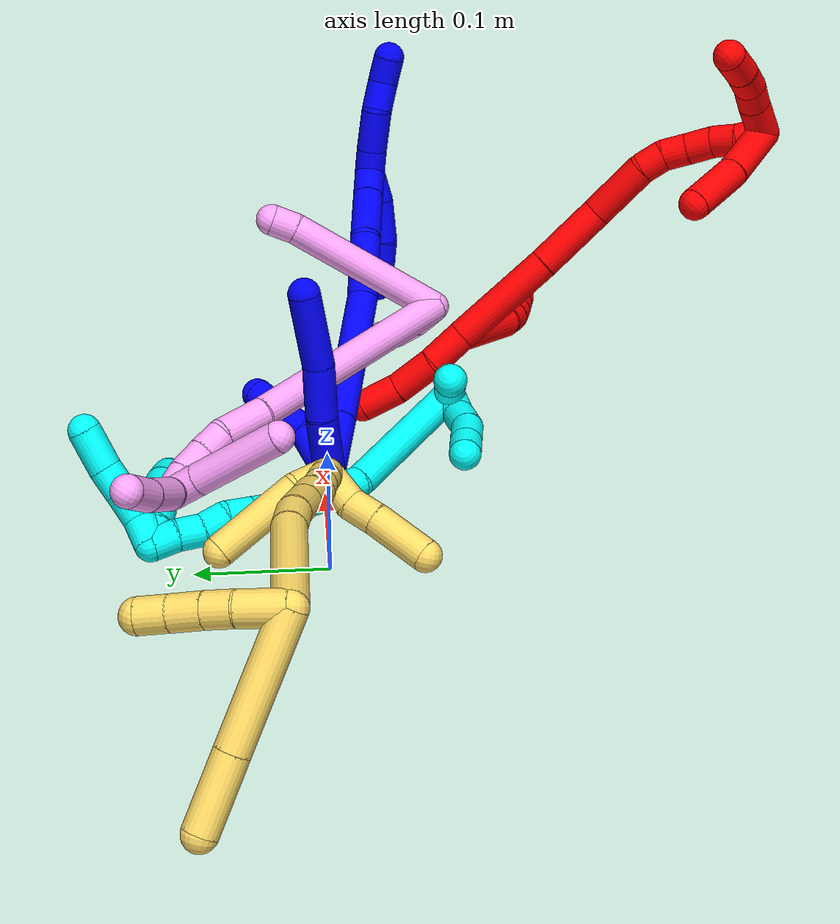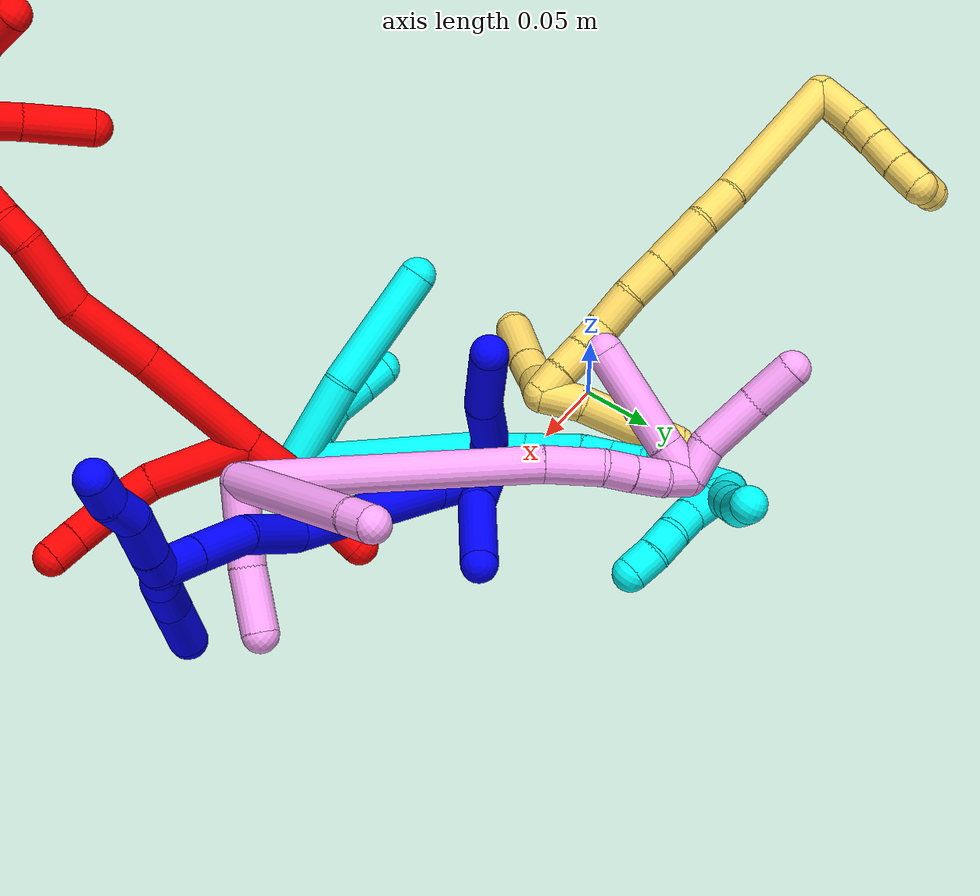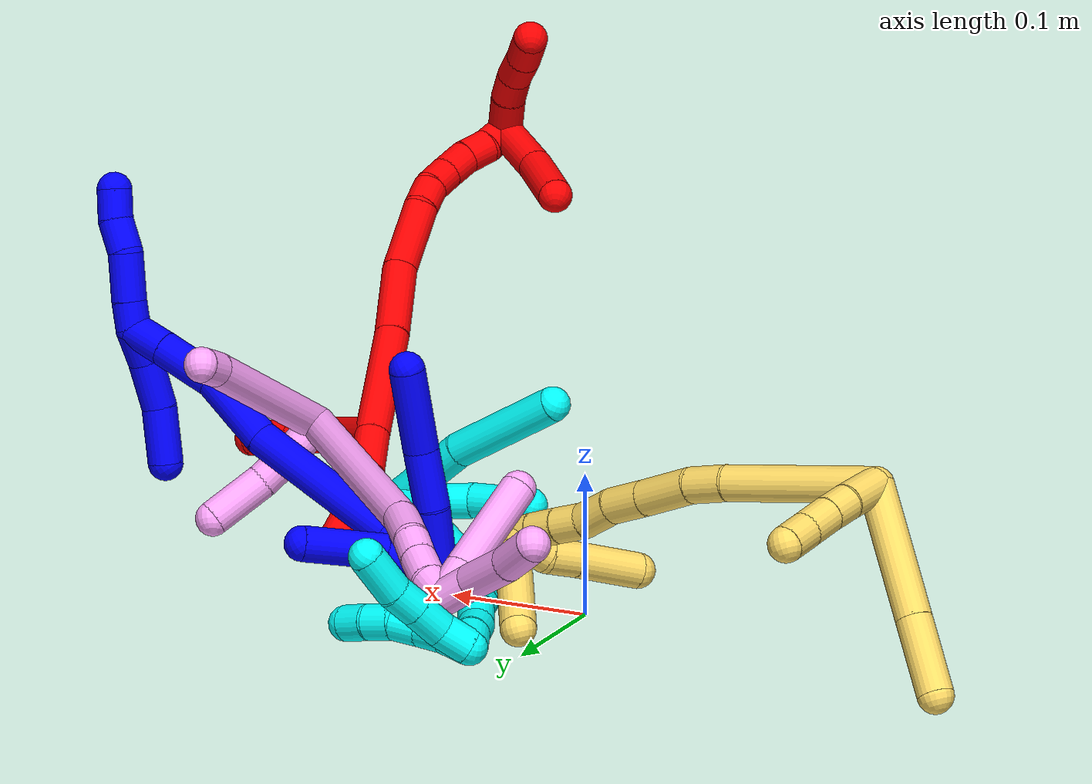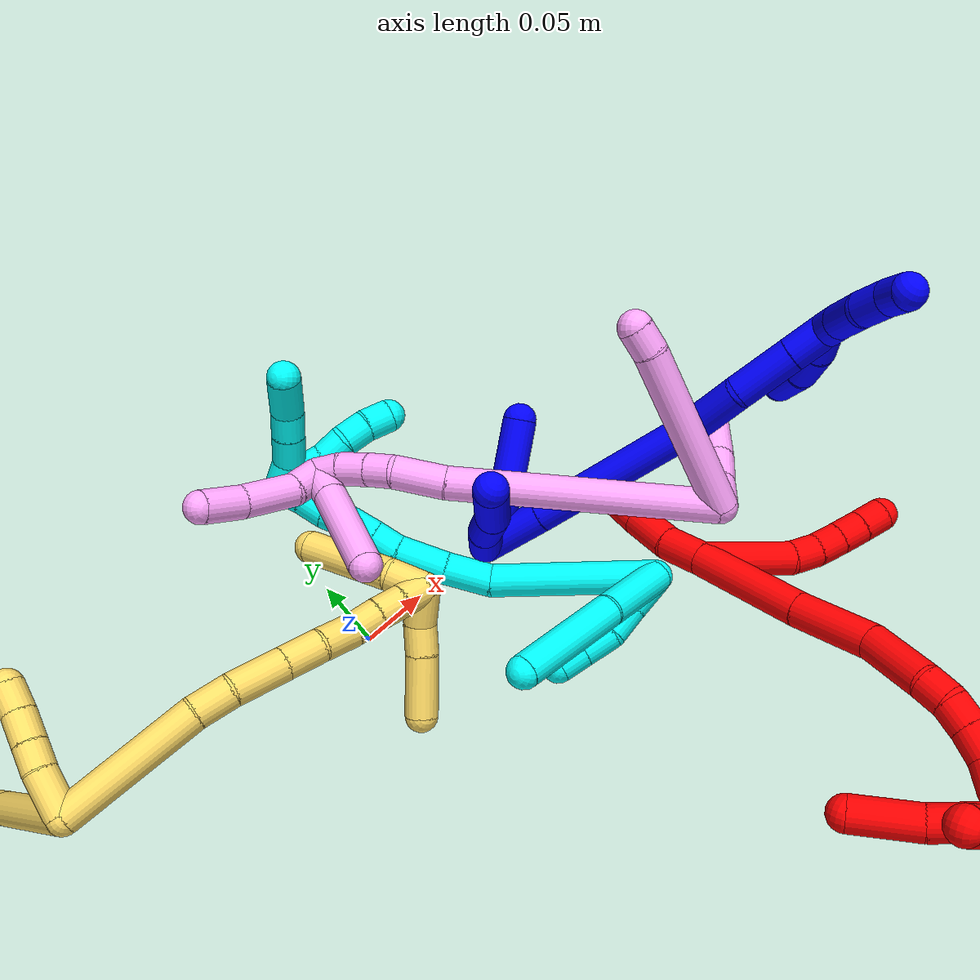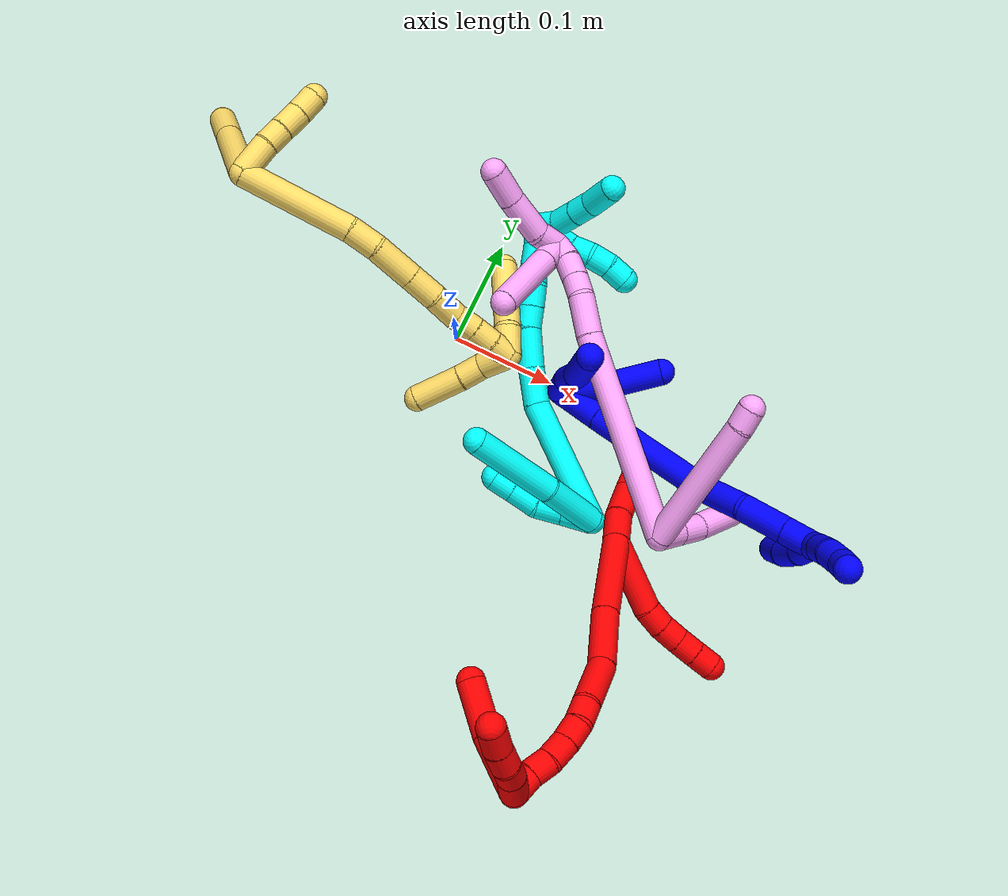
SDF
<sdf version="1.7">
 <world name="default">
  <plugin name="TubeGeneratorPlugin" filename="libtube_generator_plugin.so"/>
  <model name="photoneo_s_sensor">
   <static>1</static>
   <pose>0 0 2 1.57079 1.57079 3.14159</pose>
   <link name="link">
    <inertial><mass>0.1</mass></inertial>
    <sensor name="sensor" type="depth">
     <update_rate>30</update_rate>
     <camera>
      <horizontal_fov>1.22</horizontal_fov>
      <image><width>1920</width><height>1200</height><format>B8G8R8</format></image>
      <clip><near>0.1</near><far>4</far></clip>
      <depth_camera><output>points</output></depth_camera>
     </camera>
     <plugin name="camera_plugin" filename="libgazebo_ros_depth_camera.so">
      <baseline>0.2</baseline>
      <alwaysOn>1</alwaysOn>
      <updateRate>0.0</updateRate>
      <cameraName>camera_ir</cameraName>
      <imageTopicName>/camera/color/image_raw</imageTopicName>
      <cameraInfoTopicName>/camera/color/camera_info</cameraInfoTopicName>
      <depthImageTopicName>/camera/depth/image_raw</depthImageTopicName>
      <depthImageCameraInfoTopicName>/camera/depth/camera_info</depthImageCameraInfoTopicName>
      <pointCloudTopicName>/camera/depth/points</pointCloudTopicName>
      <frameName>fr_optical</frameName>
      <pointCloudCutoff>0.1</pointCloudCutoff>
      <pointCloudCutoffMax>2.0</pointCloudCutoffMax>
      <distortionK1>0</distortionK1>
      <distortionK2>0</distortionK2>
      <distortionK3>0</distortionK3>
      <distortionT1>0</distortionT1>
      <distortionT2>0</distortionT2>
      <CxPrime>0</CxPrime>
      <Cx>0</Cx>
      <Cy>0</Cy>
      <focalLength>0</focalLength>
      <hackBaseline>0</hackBaseline>
     </plugin>
    </sensor>
   </link>
  </model>
  <gravity>0 0 -9.8</gravity>
  <magnetic_field>6e-06 2.3e-05 -4.2e-05</magnetic_field>
  <atmosphere type="adiabatic"/>
  <physics name="default_physics" default="0" type="ode">
   <max_step_size>0.003</max_step_size>
   <real_time_factor>1</real_time_factor>
   <real_time_update_rate>1000</real_time_update_rate>
   <max_contacts>10000</max_contacts>
   <ode>
    <solver>
     <type>quick</type>
     <iters>100</iters>
     <sor>1.3</sor>
     <use_dynamic_moi_rescaling>0</use_dynamic_moi_rescaling>
    </solver>
    <constraints>
     <contact_max_correcting_vel>0</contact_max_correcting_vel>
     <contact_surface_layer>0.001</contact_surface_layer>
     <cfm>0</cfm>
     <erp>0.2</erp>
    </constraints>
   </ode>
  </physics>
  <scene><ambient>0.4 0.4 0.4 1</ambient><background>0.7 0.7 0.7 1</background><shadows>0</shadows></scene>
  <audio><device>default</device></audio>
  <spherical_coordinates>
   <surface_model>EARTH_WGS84</surface_model>
   <latitude_deg>0</latitude_deg>
   <longitude_deg>0</longitude_deg>
   <elevation>0</elevation>
   <heading_deg>0</heading_deg>
  </spherical_coordinates>
  <model name="bin">
   <static>1</static>
   <link name="bottom">
    <collision name="collision-bottom">
     <pose>0 0 -0.01 0 -0 0</pose>
     <geometry><box><size>0.8 0.6 0.02</size></box></geometry>
     <surface>
      <friction><ode><mu>100</mu><mu2>100</mu2></ode></friction>
      <contact><collide_bitmask>65535</collide_bitmask></contact>
     </surface>
    </collision>
   </link>
   <link name="west_wall">
    <collision name="collision-west_wall">
     <pose>-0.41 0 0.1 0 -0 0</pose>
     <geometry><box><size>0.02 0.6 0.2</size></box></geometry>
     <surface>
      <friction><ode><mu>100</mu><mu2>100</mu2></ode></friction>
      <contact><collide_bitmask>65535</collide_bitmask></contact>
     </surface>
    </collision>
   </link>
   <link name="east_wall">
    <collision name="collision-east_wall">
     <pose>0.41 0 0.1 0 -0 0</pose>
     <geometry><box><size>0.02 0.6 0.2</size></box></geometry>
     <surface>
      <friction><ode><mu>100</mu><mu2>100</mu2></ode></friction>
      <contact><collide_bitmask>65535</collide_bitmask></contact>
     </surface>
    </collision>
   </link>
   <link name="south_wall">
    <collision name="collision-south_wall">
     <pose>0 -0.31 0.1 0 -0 0</pose>
     <geometry><box><size>0.8 0.02 0.2</size></box></geometry>
     <surface>
      <friction><ode><mu>100</mu><mu2>100</mu2></ode></friction>
      <contact><collide_bitmask>65535</collide_bitmask></contact>
     </surface>
    </collision>
   </link>
   <link name="north_wall">
    <collision name="collision-north_wall">
     <pose>0 0.31 0.1 0 -0 0</pose>
     <geometry><box><size>0.8 0.02 0.2</size></box></geometry>
     <surface>
      <friction><ode><mu>100</mu><mu2>100</mu2></ode></friction>
      <contact><collide_bitmask>65535</collide_bitmask></contact>
     </surface>
    </collision>
   </link>
  </model>
  <model name="1">
   <static>0</static>
   <link name="1">
    <collision name="collision-cylinder-e_1_2_8">
     <pose>-0.011889 -0.000995 0.02131 0.046636 -0.508444 -0.01212</pose>
     <geometry><cylinder><radius>0.0125</radius><length>0.048845</length></cylinder></geometry>
     <surface>
      <friction><ode><mu>1.16</mu><mu2>1.16</mu2><slip1>0</slip1><slip2>0</slip2></ode></friction>
      <contact><ode><kp>1e+06</kp><kd>1</kd><max_vel>0</max_vel><min_depth>0.001</min_depth></ode></contact>
     </surface>
    </collision>
    <visual name="visual-cylinder-e_1_2_8">
     <pose>-0.011889 -0.000995 0.02131 0.046636 -0.508444 -0.01212</pose>
     <geometry><cylinder><radius>0.0125</radius><length>0.048845</length></cylinder></geometry>
     <material><ambient>0 0 1 1</ambient></material>
    </visual>
    <collision name="collision-cylinder-e_2_8_9">
     <pose>-0.031495 -0.004301 0.061838 0.119703 -0.379322 -0.023006</pose>
     <geometry><cylinder><radius>0.0125</radius><length>0.041677</length></cylinder></geometry>
     <surface>
      <friction><ode><mu>1.16</mu><mu2>1.16</mu2><slip1>0</slip1><slip2>0</slip2></ode></friction>
      <contact><ode><kp>1e+06</kp><kd>1</kd><max_vel>0</max_vel><min_depth>0.001</min_depth></ode></contact>
     </surface>
    </collision>
    <visual name="visual-cylinder-e_2_8_9">
     <pose>-0.031495 -0.004301 0.061838 0.119703 -0.379322 -0.023006</pose>
     <geometry><cylinder><radius>0.0125</radius><length>0.041677</length></cylinder></geometry>
     <material><ambient>0 0 1 1</ambient></material>
    </visual>
    <collision name="collision-cylinder-e_3_9_6">
     <pose>-0.052937 -0.006141 0.107435 -0.017842 -0.479726 0.004364</pose>
     <geometry><cylinder><radius>0.0125</radius><length>0.059479</length></cylinder></geometry>
     <surface>
      <friction><ode><mu>1.16</mu><mu2>1.16</mu2><slip1>0</slip1><slip2>0</slip2></ode></friction>
      <contact><ode><kp>1e+06</kp><kd>1</kd><max_vel>0</max_vel><min_depth>0.001</min_depth></ode></contact>
     </surface>
    </collision>
    <visual name="visual-cylinder-e_3_9_6">
     <pose>-0.052937 -0.006141 0.107435 -0.017842 -0.479726 0.004364</pose>
     <geometry><cylinder><radius>0.0125</radius><length>0.059479</length></cylinder></geometry>
     <material><ambient>0 0 1 1</ambient></material>
    </visual>
    <collision name="collision-cylinder-e_1_2_10">
     <pose>0.008623 0.00757 0.016893 -0.421283 0.435937 -0.094643</pose>
     <geometry><cylinder><radius>0.0125</radius><length>0.040844</length></cylinder></geometry>
     <surface>
      <friction><ode><mu>1.16</mu><mu2>1.16</mu2><slip1>0</slip1><slip2>0</slip2></ode></friction>
      <contact><ode><kp>1e+06</kp><kd>1</kd><max_vel>0</max_vel><min_depth>0.001</min_depth></ode></contact>
     </surface>
    </collision>
    <visual name="visual-cylinder-e_1_2_10">
     <pose>0.008623 0.00757 0.016893 -0.421283 0.435937 -0.094643</pose>
     <geometry><cylinder><radius>0.0125</radius><length>0.040844</length></cylinder></geometry>
     <material><ambient>0 0 1 1</ambient></material>
    </visual>
    <collision name="collision-cylinder-e_2_10_5">
     <pose>0.031921 0.033043 0.0522 -0.771336 0.519126 -0.2148</pose>
     <geometry><cylinder><radius>0.0125</radius><length>0.059156</length></cylinder></geometry>
     <surface>
      <friction><ode><mu>1.16</mu><mu2>1.16</mu2><slip1>0</slip1><slip2>0</slip2></ode></friction>
      <contact><ode><kp>1e+06</kp><kd>1</kd><max_vel>0</max_vel><min_depth>0.001</min_depth></ode></contact>
     </surface>
    </collision>
    <visual name="visual-cylinder-e_2_10_5">
     <pose>0.031921 0.033043 0.0522 -0.771336 0.519126 -0.2148</pose>
     <geometry><cylinder><radius>0.0125</radius><length>0.059156</length></cylinder></geometry>
     <material><ambient>0 0 1 1</ambient></material>
    </visual>
    <collision name="collision-cylinder-e_1_2_11">
     <pose>0.013935 -0.00619 0.020057 0.299368 0.586082 0.090946</pose>
     <geometry><cylinder><radius>0.0125</radius><length>0.05039</length></cylinder></geometry>
     <surface>
      <friction><ode><mu>1.16</mu><mu2>1.16</mu2><slip1>0</slip1><slip2>0</slip2></ode></friction>
      <contact><ode><kp>1e+06</kp><kd>1</kd><max_vel>0</max_vel><min_depth>0.001</min_depth></ode></contact>
     </surface>
    </collision>
    <visual name="visual-cylinder-e_1_2_11">
     <pose>0.013935 -0.00619 0.020057 0.299368 0.586082 0.090946</pose>
     <geometry><cylinder><radius>0.0125</radius><length>0.05039</length></cylinder></geometry>
     <material><ambient>0 0 1 1</ambient></material>
    </visual>
    <collision name="collision-cylinder-e_2_11_12">
     <pose>0.062508 -0.026444 0.089133 0.279379 0.596632 0.086416</pose>
     <geometry><cylinder><radius>0.0125</radius><length>0.123296</length></cylinder></geometry>
     <surface>
      <friction><ode><mu>1.16</mu><mu2>1.16</mu2><slip1>0</slip1><slip2>0</slip2></ode></friction>
      <contact><ode><kp>1e+06</kp><kd>1</kd><max_vel>0</max_vel><min_depth>0.001</min_depth></ode></contact>
     </surface>
    </collision>
    <visual name="visual-cylinder-e_2_11_12">
     <pose>0.062508 -0.026444 0.089133 0.279379 0.596632 0.086416</pose>
     <geometry><cylinder><radius>0.0125</radius><length>0.123296</length></cylinder></geometry>
     <material><ambient>0 0 1 1</ambient></material>
    </visual>
    <collision name="collision-cylinder-e_3_12_13">
     <pose>0.104884 -0.045065 0.163546 0.177619 0.291421 0.026133</pose>
     <geometry><cylinder><radius>0.0125</radius><length>0.053869</length></cylinder></geometry>
     <surface>
      <friction><ode><mu>1.16</mu><mu2>1.16</mu2><slip1>0</slip1><slip2>0</slip2></ode></friction>
      <contact><ode><kp>1e+06</kp><kd>1</kd><max_vel>0</max_vel><min_depth>0.001</min_depth></ode></contact>
     </surface>
    </collision>
    <visual name="visual-cylinder-e_3_12_13">
     <pose>0.104884 -0.045065 0.163546 0.177619 0.291421 0.026133</pose>
     <geometry><cylinder><radius>0.0125</radius><length>0.053869</length></cylinder></geometry>
     <material><ambient>0 0 1 1</ambient></material>
    </visual>
    <collision name="collision-cylinder-e_4_13_14">
     <pose>0.125353 -0.052618 0.206815 0.165998 0.612294 0.052578</pose>
     <geometry><cylinder><radius>0.0125</radius><length>0.044298</length></cylinder></geometry>
     <surface>
      <friction><ode><mu>1.16</mu><mu2>1.16</mu2><slip1>0</slip1><slip2>0</slip2></ode></friction>
      <contact><ode><kp>1e+06</kp><kd>1</kd><max_vel>0</max_vel><min_depth>0.001</min_depth></ode></contact>
     </surface>
    </collision>
    <visual name="visual-cylinder-e_4_13_14">
     <pose>0.125353 -0.052618 0.206815 0.165998 0.612294 0.052578</pose>
     <geometry><cylinder><radius>0.0125</radius><length>0.044298</length></cylinder></geometry>
     <material><ambient>0 0 1 1</ambient></material>
    </visual>
    <collision name="collision-cylinder-e_5_14_1">
     <pose>0.146477 -0.05749 0.23583 0.166937 0.639074 0.05535</pose>
     <geometry><cylinder><radius>0.0125</radius><length>0.028147</length></cylinder></geometry>
     <surface>
      <friction><ode><mu>1.16</mu><mu2>1.16</mu2><slip1>0</slip1><slip2>0</slip2></ode></friction>
      <contact><ode><kp>1e+06</kp><kd>1</kd><max_vel>0</max_vel><min_depth>0.001</min_depth></ode></contact>
     </surface>
    </collision>
    <visual name="visual-cylinder-e_5_14_1">
     <pose>0.146477 -0.05749 0.23583 0.166937 0.639074 0.05535</pose>
     <geometry><cylinder><radius>0.0125</radius><length>0.028147</length></cylinder></geometry>
     <material><ambient>0 0 1 1</ambient></material>
    </visual>
    <collision name="collision-cylinder-e_1_1_15">
     <pose>0.159174 -0.060969 0.23518 3.00657 0.347015 2.40524</pose>
     <geometry><cylinder><radius>0.0125</radius><length>0.025304</length></cylinder></geometry>
     <surface>
      <friction><ode><mu>1.16</mu><mu2>1.16</mu2><slip1>0</slip1><slip2>0</slip2></ode></friction>
      <contact><ode><kp>1e+06</kp><kd>1</kd><max_vel>0</max_vel><min_depth>0.001</min_depth></ode></contact>
     </surface>
    </collision>
    <visual name="visual-cylinder-e_1_1_15">
     <pose>0.159174 -0.060969 0.23518 3.00657 0.347015 2.40524</pose>
     <geometry><cylinder><radius>0.0125</radius><length>0.025304</length></cylinder></geometry>
     <material><ambient>0 0 1 1</ambient></material>
    </visual>
    <collision name="collision-cylinder-e_2_15_16">
     <pose>0.168788 -0.061668 0.206984 -3.08662 0.312639 -2.7962</pose>
     <geometry><cylinder><radius>0.0125</radius><length>0.034536</length></cylinder></geometry>
     <surface>
      <friction><ode><mu>1.16</mu><mu2>1.16</mu2><slip1>0</slip1><slip2>0</slip2></ode></friction>
      <contact><ode><kp>1e+06</kp><kd>1</kd><max_vel>0</max_vel><min_depth>0.001</min_depth></ode></contact>
     </surface>
    </collision>
    <visual name="visual-cylinder-e_2_15_16">
     <pose>0.168788 -0.061668 0.206984 -3.08662 0.312639 -2.7962</pose>
     <geometry><cylinder><radius>0.0125</radius><length>0.034536</length></cylinder></geometry>
     <material><ambient>0 0 1 1</ambient></material>
    </visual>
    <collision name="collision-cylinder-e_3_16_4">
     <pose>0.181552 -0.055882 0.172583 -2.87665 0.380257 -1.93041</pose>
     <geometry><cylinder><radius>0.0125</radius><length>0.04016</length></cylinder></geometry>
     <surface>
      <friction><ode><mu>1.16</mu><mu2>1.16</mu2><slip1>0</slip1><slip2>0</slip2></ode></friction>
      <contact><ode><kp>1e+06</kp><kd>1</kd><max_vel>0</max_vel><min_depth>0.001</min_depth></ode></contact>
     </surface>
    </collision>
    <visual name="visual-cylinder-e_3_16_4">
     <pose>0.181552 -0.055882 0.172583 -2.87665 0.380257 -1.93041</pose>
     <geometry><cylinder><radius>0.0125</radius><length>0.04016</length></cylinder></geometry>
     <material><ambient>0 0 1 1</ambient></material>
    </visual>
    <collision name="collision-cylinder-e_1_1_17">
     <pose>0.151508 -0.061804 0.256156 0.259282 -0.340098 -0.044764</pose>
     <geometry><cylinder><radius>0.0125</radius><length>0.020164</length></cylinder></geometry>
     <surface>
      <friction><ode><mu>1.16</mu><mu2>1.16</mu2><slip1>0</slip1><slip2>0</slip2></ode></friction>
      <contact><ode><kp>1e+06</kp><kd>1</kd><max_vel>0</max_vel><min_depth>0.001</min_depth></ode></contact>
     </surface>
    </collision>
    <visual name="visual-cylinder-e_1_1_17">
     <pose>0.151508 -0.061804 0.256156 0.259282 -0.340098 -0.044764</pose>
     <geometry><cylinder><radius>0.0125</radius><length>0.020164</length></cylinder></geometry>
     <material><ambient>0 0 1 1</ambient></material>
    </visual>
    <collision name="collision-cylinder-e_2_17_18">
     <pose>0.1415 -0.068979 0.280377 0.305335 -0.398985 -0.062197</pose>
     <geometry><cylinder><radius>0.0125</radius><length>0.034212</length></cylinder></geometry>
     <surface>
      <friction><ode><mu>1.16</mu><mu2>1.16</mu2><slip1>0</slip1><slip2>0</slip2></ode></friction>
      <contact><ode><kp>1e+06</kp><kd>1</kd><max_vel>0</max_vel><min_depth>0.001</min_depth></ode></contact>
     </surface>
    </collision>
    <visual name="visual-cylinder-e_2_17_18">
     <pose>0.1415 -0.068979 0.280377 0.305335 -0.398985 -0.062197</pose>
     <geometry><cylinder><radius>0.0125</radius><length>0.034212</length></cylinder></geometry>
     <material><ambient>0 0 1 1</ambient></material>
    </visual>
    <collision name="collision-cylinder-e_3_18_19">
     <pose>0.134158 -0.078023 0.306566 0.368332 -0.058203 -0.010845</pose>
     <geometry><cylinder><radius>0.0125</radius><length>0.023957</length></cylinder></geometry>
     <surface>
      <friction><ode><mu>1.16</mu><mu2>1.16</mu2><slip1>0</slip1><slip2>0</slip2></ode></friction>
      <contact><ode><kp>1e+06</kp><kd>1</kd><max_vel>0</max_vel><min_depth>0.001</min_depth></ode></contact>
     </surface>
    </collision>
    <visual name="visual-cylinder-e_3_18_19">
     <pose>0.134158 -0.078023 0.306566 0.368332 -0.058203 -0.010845</pose>
     <geometry><cylinder><radius>0.0125</radius><length>0.023957</length></cylinder></geometry>
     <material><ambient>0 0 1 1</ambient></material>
    </visual>
    <collision name="collision-cylinder-e_4_19_3">
     <pose>0.129722 -0.086469 0.327009 0.41935 -0.352386 -0.075738</pose>
     <geometry><cylinder><radius>0.0125</radius><length>0.021667</length></cylinder></geometry>
     <surface>
      <friction><ode><mu>1.16</mu><mu2>1.16</mu2><slip1>0</slip1><slip2>0</slip2></ode></friction>
      <contact><ode><kp>1e+06</kp><kd>1</kd><max_vel>0</max_vel><min_depth>0.001</min_depth></ode></contact>
     </surface>
    </collision>
    <visual name="visual-cylinder-e_4_19_3">
     <pose>0.129722 -0.086469 0.327009 0.41935 -0.352386 -0.075738</pose>
     <geometry><cylinder><radius>0.0125</radius><length>0.021667</length></cylinder></geometry>
     <material><ambient>0 0 1 1</ambient></material>
    </visual>
    <collision name="collision-sphere-3">
     <pose>0.125983 -0.090609 0.336296 0 -0 0</pose>
     <geometry><sphere><radius>0.0125</radius></sphere></geometry>
     <surface>
      <friction><ode><mu>1.16</mu><mu2>1.16</mu2><slip1>0</slip1><slip2>0</slip2></ode></friction>
      <contact><ode><kp>1e+06</kp><kd>1</kd><max_vel>0</max_vel><min_depth>0.001</min_depth></ode></contact>
     </surface>
    </collision>
    <visual name="visual-sphere-3">
     <pose>0.125983 -0.090609 0.336296 0 -0 0</pose>
     <geometry><sphere><radius>0.0125</radius></sphere></geometry>
     <material><ambient>0 0 1 1</ambient></material>
    </visual>
    <collision name="collision-sphere-19">
     <pose>0.133461 -0.082329 0.317723 0 -0 0</pose>
     <geometry><sphere><radius>0.0125</radius></sphere></geometry>
     <surface>
      <friction><ode><mu>1.16</mu><mu2>1.16</mu2><slip1>0</slip1><slip2>0</slip2></ode></friction>
      <contact><ode><kp>1e+06</kp><kd>1</kd><max_vel>0</max_vel><min_depth>0.001</min_depth></ode></contact>
     </surface>
    </collision>
    <visual name="visual-sphere-19">
     <pose>0.133461 -0.082329 0.317723 0 -0 0</pose>
     <geometry><sphere><radius>0.0125</radius></sphere></geometry>
     <material><ambient>0 0 1 1</ambient></material>
    </visual>
    <collision name="collision-sphere-5">
     <pose>0.046595 0.050945 0.070613 0 -0 0</pose>
     <geometry><sphere><radius>0.0125</radius></sphere></geometry>
     <surface>
      <friction><ode><mu>1.16</mu><mu2>1.16</mu2><slip1>0</slip1><slip2>0</slip2></ode></friction>
      <contact><ode><kp>1e+06</kp><kd>1</kd><max_vel>0</max_vel><min_depth>0.001</min_depth></ode></contact>
     </surface>
    </collision>
    <visual name="visual-sphere-5">
     <pose>0.046595 0.050945 0.070613 0 -0 0</pose>
     <geometry><sphere><radius>0.0125</radius></sphere></geometry>
     <material><ambient>0 0 1 1</ambient></material>
    </visual>
    <collision name="collision-sphere-10">
     <pose>0.017247 0.01514 0.033787 0 -0 0</pose>
     <geometry><sphere><radius>0.0125</radius></sphere></geometry>
     <surface>
      <friction><ode><mu>1.16</mu><mu2>1.16</mu2><slip1>0</slip1><slip2>0</slip2></ode></friction>
      <contact><ode><kp>1e+06</kp><kd>1</kd><max_vel>0</max_vel><min_depth>0.001</min_depth></ode></contact>
     </surface>
    </collision>
    <visual name="visual-sphere-10">
     <pose>0.017247 0.01514 0.033787 0 -0 0</pose>
     <geometry><sphere><radius>0.0125</radius></sphere></geometry>
     <material><ambient>0 0 1 1</ambient></material>
    </visual>
    <collision name="collision-sphere-6">
     <pose>-0.066663 -0.005671 0.133813 0 -0 0</pose>
     <geometry><sphere><radius>0.0125</radius></sphere></geometry>
     <surface>
      <friction><ode><mu>1.16</mu><mu2>1.16</mu2><slip1>0</slip1><slip2>0</slip2></ode></friction>
      <contact><ode><kp>1e+06</kp><kd>1</kd><max_vel>0</max_vel><min_depth>0.001</min_depth></ode></contact>
     </surface>
    </collision>
    <visual name="visual-sphere-6">
     <pose>-0.066663 -0.005671 0.133813 0 -0 0</pose>
     <geometry><sphere><radius>0.0125</radius></sphere></geometry>
     <material><ambient>0 0 1 1</ambient></material>
    </visual>
    <collision name="collision-sphere-9">
     <pose>-0.039211 -0.006612 0.081057 0 -0 0</pose>
     <geometry><sphere><radius>0.0125</radius></sphere></geometry>
     <surface>
      <friction><ode><mu>1.16</mu><mu2>1.16</mu2><slip1>0</slip1><slip2>0</slip2></ode></friction>
      <contact><ode><kp>1e+06</kp><kd>1</kd><max_vel>0</max_vel><min_depth>0.001</min_depth></ode></contact>
     </surface>
    </collision>
    <visual name="visual-sphere-9">
     <pose>-0.039211 -0.006612 0.081057 0 -0 0</pose>
     <geometry><sphere><radius>0.0125</radius></sphere></geometry>
     <material><ambient>0 0 1 1</ambient></material>
    </visual>
    <collision name="collision-sphere-2">
     <geometry><sphere><radius>0.0125</radius></sphere></geometry>
     <surface>
      <friction><ode><mu>1.16</mu><mu2>1.16</mu2><slip1>0</slip1><slip2>0</slip2></ode></friction>
      <contact><ode><kp>1e+06</kp><kd>1</kd><max_vel>0</max_vel><min_depth>0.001</min_depth></ode></contact>
     </surface>
    </collision>
    <visual name="visual-sphere-2">
     <geometry><sphere><radius>0.0125</radius></sphere></geometry>
     <material><ambient>0 0 1 1</ambient></material>
    </visual>
    <collision name="collision-sphere-8">
     <pose>-0.023779 -0.001989 0.04262 0 -0 0</pose>
     <geometry><sphere><radius>0.0125</radius></sphere></geometry>
     <surface>
      <friction><ode><mu>1.16</mu><mu2>1.16</mu2><slip1>0</slip1><slip2>0</slip2></ode></friction>
      <contact><ode><kp>1e+06</kp><kd>1</kd><max_vel>0</max_vel><min_depth>0.001</min_depth></ode></contact>
     </surface>
    </collision>
    <visual name="visual-sphere-8">
     <pose>-0.023779 -0.001989 0.04262 0 -0 0</pose>
     <geometry><sphere><radius>0.0125</radius></sphere></geometry>
     <material><ambient>0 0 1 1</ambient></material>
    </visual>
    <collision name="collision-sphere-11">
     <pose>0.027871 -0.012381 0.040114 0 -0 0</pose>
     <geometry><sphere><radius>0.0125</radius></sphere></geometry>
     <surface>
      <friction><ode><mu>1.16</mu><mu2>1.16</mu2><slip1>0</slip1><slip2>0</slip2></ode></friction>
      <contact><ode><kp>1e+06</kp><kd>1</kd><max_vel>0</max_vel><min_depth>0.001</min_depth></ode></contact>
     </surface>
    </collision>
    <visual name="visual-sphere-11">
     <pose>0.027871 -0.012381 0.040114 0 -0 0</pose>
     <geometry><sphere><radius>0.0125</radius></sphere></geometry>
     <material><ambient>0 0 1 1</ambient></material>
    </visual>
    <collision name="collision-sphere-12">
     <pose>0.097146 -0.040507 0.138153 0 -0 0</pose>
     <geometry><sphere><radius>0.0125</radius></sphere></geometry>
     <surface>
      <friction><ode><mu>1.16</mu><mu2>1.16</mu2><slip1>0</slip1><slip2>0</slip2></ode></friction>
      <contact><ode><kp>1e+06</kp><kd>1</kd><max_vel>0</max_vel><min_depth>0.001</min_depth></ode></contact>
     </surface>
    </collision>
    <visual name="visual-sphere-12">
     <pose>0.097146 -0.040507 0.138153 0 -0 0</pose>
     <geometry><sphere><radius>0.0125</radius></sphere></geometry>
     <material><ambient>0 0 1 1</ambient></material>
    </visual>
    <collision name="collision-sphere-13">
     <pose>0.112623 -0.049623 0.188939 0 -0 0</pose>
     <geometry><sphere><radius>0.0125</radius></sphere></geometry>
     <surface>
      <friction><ode><mu>1.16</mu><mu2>1.16</mu2><slip1>0</slip1><slip2>0</slip2></ode></friction>
      <contact><ode><kp>1e+06</kp><kd>1</kd><max_vel>0</max_vel><min_depth>0.001</min_depth></ode></contact>
     </surface>
    </collision>
    <visual name="visual-sphere-13">
     <pose>0.112623 -0.049623 0.188939 0 -0 0</pose>
     <geometry><sphere><radius>0.0125</radius></sphere></geometry>
     <material><ambient>0 0 1 1</ambient></material>
    </visual>
    <collision name="collision-sphere-14">
     <pose>0.138083 -0.055613 0.224691 0 -0 0</pose>
     <geometry><sphere><radius>0.0125</radius></sphere></geometry>
     <surface>
      <friction><ode><mu>1.16</mu><mu2>1.16</mu2><slip1>0</slip1><slip2>0</slip2></ode></friction>
      <contact><ode><kp>1e+06</kp><kd>1</kd><max_vel>0</max_vel><min_depth>0.001</min_depth></ode></contact>
     </surface>
    </collision>
    <visual name="visual-sphere-14">
     <pose>0.138083 -0.055613 0.224691 0 -0 0</pose>
     <geometry><sphere><radius>0.0125</radius></sphere></geometry>
     <material><ambient>0 0 1 1</ambient></material>
    </visual>
    <collision name="collision-sphere-1">
     <pose>0.154872 -0.059367 0.246969 0 -0 0</pose>
     <geometry><sphere><radius>0.0125</radius></sphere></geometry>
     <surface>
      <friction><ode><mu>1.16</mu><mu2>1.16</mu2><slip1>0</slip1><slip2>0</slip2></ode></friction>
      <contact><ode><kp>1e+06</kp><kd>1</kd><max_vel>0</max_vel><min_depth>0.001</min_depth></ode></contact>
     </surface>
    </collision>
    <visual name="visual-sphere-1">
     <pose>0.154872 -0.059367 0.246969 0 -0 0</pose>
     <geometry><sphere><radius>0.0125</radius></sphere></geometry>
     <material><ambient>0 0 1 1</ambient></material>
    </visual>
    <collision name="collision-sphere-18">
     <pose>0.134854 -0.073718 0.29541 0 -0 0</pose>
     <geometry><sphere><radius>0.0125</radius></sphere></geometry>
     <surface>
      <friction><ode><mu>1.16</mu><mu2>1.16</mu2><slip1>0</slip1><slip2>0</slip2></ode></friction>
      <contact><ode><kp>1e+06</kp><kd>1</kd><max_vel>0</max_vel><min_depth>0.001</min_depth></ode></contact>
     </surface>
    </collision>
    <visual name="visual-sphere-18">
     <pose>0.134854 -0.073718 0.29541 0 -0 0</pose>
     <geometry><sphere><radius>0.0125</radius></sphere></geometry>
     <material><ambient>0 0 1 1</ambient></material>
    </visual>
    <collision name="collision-sphere-15">
     <pose>0.163477 -0.06257 0.22339 0 -0 0</pose>
     <geometry><sphere><radius>0.0125</radius></sphere></geometry>
     <surface>
      <friction><ode><mu>1.16</mu><mu2>1.16</mu2><slip1>0</slip1><slip2>0</slip2></ode></friction>
      <contact><ode><kp>1e+06</kp><kd>1</kd><max_vel>0</max_vel><min_depth>0.001</min_depth></ode></contact>
     </surface>
    </collision>
    <visual name="visual-sphere-15">
     <pose>0.163477 -0.06257 0.22339 0 -0 0</pose>
     <geometry><sphere><radius>0.0125</radius></sphere></geometry>
     <material><ambient>0 0 1 1</ambient></material>
    </visual>
    <collision name="collision-sphere-16">
     <pose>0.174099 -0.060765 0.190578 0 -0 0</pose>
     <geometry><sphere><radius>0.0125</radius></sphere></geometry>
     <surface>
      <friction><ode><mu>1.16</mu><mu2>1.16</mu2><slip1>0</slip1><slip2>0</slip2></ode></friction>
      <contact><ode><kp>1e+06</kp><kd>1</kd><max_vel>0</max_vel><min_depth>0.001</min_depth></ode></contact>
     </surface>
    </collision>
    <visual name="visual-sphere-16">
     <pose>0.174099 -0.060765 0.190578 0 -0 0</pose>
     <geometry><sphere><radius>0.0125</radius></sphere></geometry>
     <material><ambient>0 0 1 1</ambient></material>
    </visual>
    <collision name="collision-sphere-4">
     <pose>0.189005 -0.051 0.154588 0 -0 0</pose>
     <geometry><sphere><radius>0.0125</radius></sphere></geometry>
     <surface>
      <friction><ode><mu>1.16</mu><mu2>1.16</mu2><slip1>0</slip1><slip2>0</slip2></ode></friction>
      <contact><ode><kp>1e+06</kp><kd>1</kd><max_vel>0</max_vel><min_depth>0.001</min_depth></ode></contact>
     </surface>
    </collision>
    <visual name="visual-sphere-4">
     <pose>0.189005 -0.051 0.154588 0 -0 0</pose>
     <geometry><sphere><radius>0.0125</radius></sphere></geometry>
     <material><ambient>0 0 1 1</ambient></material>
    </visual>
    <collision name="collision-sphere-17">
     <pose>0.148145 -0.064241 0.265343 0 -0 0</pose>
     <geometry><sphere><radius>0.0125</radius></sphere></geometry>
     <surface>
      <friction><ode><mu>1.16</mu><mu2>1.16</mu2><slip1>0</slip1><slip2>0</slip2></ode></friction>
      <contact><ode><kp>1e+06</kp><kd>1</kd><max_vel>0</max_vel><min_depth>0.001</min_depth></ode></contact>
     </surface>
    </collision>
    <visual name="visual-sphere-17">
     <pose>0.148145 -0.064241 0.265343 0 -0 0</pose>
     <geometry><sphere><radius>0.0125</radius></sphere></geometry>
     <material><ambient>0 0 1 1</ambient></material>
    </visual>
    <inertial>
     <pose>0.069337 -0.028725 0.132818 0 -0 0</pose>
     <mass>0.75</mass>
     <inertia>
      <ixx>0.00024</ixx>
      <ixy>0</ixy>
      <ixz>0</ixz>
      <iyy>0.000274</iyy>
      <iyz>0</iyz>
      <izz>-3.9e-05</izz>
     </inertia>
    </inertial>
   </link>
   <pose>0.111905 -0.00412 0.012178 -0.167585 0.568755 -0.114689</pose>
  </model>
  <model name="2">
   <static>0</static>
   <link name="2">
    <collision name="collision-cylinder-e_1_2_8">
     <pose>0.020482 0.019052 0.019681 -0.769148 0.642044 -0.267555</pose>
     <geometry><cylinder><radius>0.0125</radius><length>0.068406</length></cylinder></geometry>
     <surface>
      <friction><ode><mu>1.16</mu><mu2>1.16</mu2><slip1>0</slip1><slip2>0</slip2></ode></friction>
      <contact><ode><kp>1e+06</kp><kd>1</kd><max_vel>0</max_vel><min_depth>0.001</min_depth></ode></contact>
     </surface>
    </collision>
    <visual name="visual-cylinder-e_1_2_8">
     <pose>0.020482 0.019052 0.019681 -0.769148 0.642044 -0.267555</pose>
     <geometry><cylinder><radius>0.0125</radius><length>0.068406</length></cylinder></geometry>
     <material><ambient>1 0 0 1</ambient></material>
    </visual>
    <collision name="collision-cylinder-e_2_8_9">
     <pose>0.046241 0.046231 0.044012 -1.05122 0.513243 -0.302092</pose>
     <geometry><cylinder><radius>0.0125</radius><length>0.021496</length></cylinder></geometry>
     <surface>
      <friction><ode><mu>1.16</mu><mu2>1.16</mu2><slip1>0</slip1><slip2>0</slip2></ode></friction>
      <contact><ode><kp>1e+06</kp><kd>1</kd><max_vel>0</max_vel><min_depth>0.001</min_depth></ode></contact>
     </surface>
    </collision>
    <visual name="visual-cylinder-e_2_8_9">
     <pose>0.046241 0.046231 0.044012 -1.05122 0.513243 -0.302092</pose>
     <geometry><cylinder><radius>0.0125</radius><length>0.021496</length></cylinder></geometry>
     <material><ambient>1 0 0 1</ambient></material>
    </visual>
    <collision name="collision-cylinder-e_3_9_10">
     <pose>0.055128 0.062837 0.052584 -1.13737 0.368758 -0.237266</pose>
     <geometry><cylinder><radius>0.0125</radius><length>0.02003</length></cylinder></geometry>
     <surface>
      <friction><ode><mu>1.16</mu><mu2>1.16</mu2><slip1>0</slip1><slip2>0</slip2></ode></friction>
      <contact><ode><kp>1e+06</kp><kd>1</kd><max_vel>0</max_vel><min_depth>0.001</min_depth></ode></contact>
     </surface>
    </collision>
    <visual name="visual-cylinder-e_3_9_10">
     <pose>0.055128 0.062837 0.052584 -1.13737 0.368758 -0.237266</pose>
     <geometry><cylinder><radius>0.0125</radius><length>0.02003</length></cylinder></geometry>
     <material><ambient>1 0 0 1</ambient></material>
    </visual>
    <collision name="collision-cylinder-e_4_10_11">
     <pose>0.06197 0.079976 0.060394 -1.14901 0.328143 -0.213534</pose>
     <geometry><cylinder><radius>0.0125</radius><length>0.020057</length></cylinder></geometry>
     <surface>
      <friction><ode><mu>1.16</mu><mu2>1.16</mu2><slip1>0</slip1><slip2>0</slip2></ode></friction>
      <contact><ode><kp>1e+06</kp><kd>1</kd><max_vel>0</max_vel><min_depth>0.001</min_depth></ode></contact>
     </surface>
    </collision>
    <visual name="visual-cylinder-e_4_10_11">
     <pose>0.06197 0.079976 0.060394 -1.14901 0.328143 -0.213534</pose>
     <geometry><cylinder><radius>0.0125</radius><length>0.020057</length></cylinder></geometry>
     <material><ambient>1 0 0 1</ambient></material>
    </visual>
    <collision name="collision-cylinder-e_5_11_6">
     <pose>0.068447 0.09737 0.067932 -1.17474 0.33027 -0.220996</pose>
     <geometry><cylinder><radius>0.0125</radius><length>0.020011</length></cylinder></geometry>
     <surface>
      <friction><ode><mu>1.16</mu><mu2>1.16</mu2><slip1>0</slip1><slip2>0</slip2></ode></friction>
      <contact><ode><kp>1e+06</kp><kd>1</kd><max_vel>0</max_vel><min_depth>0.001</min_depth></ode></contact>
     </surface>
    </collision>
    <visual name="visual-cylinder-e_5_11_6">
     <pose>0.068447 0.09737 0.067932 -1.17474 0.33027 -0.220996</pose>
     <geometry><cylinder><radius>0.0125</radius><length>0.020011</length></cylinder></geometry>
     <material><ambient>1 0 0 1</ambient></material>
    </visual>
    <collision name="collision-cylinder-e_1_2_12">
     <pose>0.000296 0.001888 -0.016031 -3.02435 0.018321 -0.309668</pose>
     <geometry><cylinder><radius>0.0125</radius><length>0.032289</length></cylinder></geometry>
     <surface>
      <friction><ode><mu>1.16</mu><mu2>1.16</mu2><slip1>0</slip1><slip2>0</slip2></ode></friction>
      <contact><ode><kp>1e+06</kp><kd>1</kd><max_vel>0</max_vel><min_depth>0.001</min_depth></ode></contact>
     </surface>
    </collision>
    <visual name="visual-cylinder-e_1_2_12">
     <pose>0.000296 0.001888 -0.016031 -3.02435 0.018321 -0.309668</pose>
     <geometry><cylinder><radius>0.0125</radius><length>0.032289</length></cylinder></geometry>
     <material><ambient>1 0 0 1</ambient></material>
    </visual>
    <collision name="collision-cylinder-e_2_12_13">
     <pose>0.000965 0.009284 -0.048757 -2.82292 0.02126 -0.13211</pose>
     <geometry><cylinder><radius>0.0125</radius><length>0.035167</length></cylinder></geometry>
     <surface>
      <friction><ode><mu>1.16</mu><mu2>1.16</mu2><slip1>0</slip1><slip2>0</slip2></ode></friction>
      <contact><ode><kp>1e+06</kp><kd>1</kd><max_vel>0</max_vel><min_depth>0.001</min_depth></ode></contact>
     </surface>
    </collision>
    <visual name="visual-cylinder-e_2_12_13">
     <pose>0.000965 0.009284 -0.048757 -2.82292 0.02126 -0.13211</pose>
     <geometry><cylinder><radius>0.0125</radius><length>0.035167</length></cylinder></geometry>
     <material><ambient>1 0 0 1</ambient></material>
    </visual>
    <collision name="collision-cylinder-e_3_13_5">
     <pose>-0.001392 0.020192 -0.080556 -2.79827 -0.168645 0.907247</pose>
     <geometry><cylinder><radius>0.0125</radius><length>0.032544</length></cylinder></geometry>
     <surface>
      <friction><ode><mu>1.16</mu><mu2>1.16</mu2><slip1>0</slip1><slip2>0</slip2></ode></friction>
      <contact><ode><kp>1e+06</kp><kd>1</kd><max_vel>0</max_vel><min_depth>0.001</min_depth></ode></contact>
     </surface>
    </collision>
    <visual name="visual-cylinder-e_3_13_5">
     <pose>-0.001392 0.020192 -0.080556 -2.79827 -0.168645 0.907247</pose>
     <geometry><cylinder><radius>0.0125</radius><length>0.032544</length></cylinder></geometry>
     <material><ambient>1 0 0 1</ambient></material>
    </visual>
    <collision name="collision-cylinder-e_1_2_14">
     <pose>-0.000984 -0.007086 0.043144 0.162797 -0.022497 -0.001835</pose>
     <geometry><cylinder><radius>0.0125</radius><length>0.087466</length></cylinder></geometry>
     <surface>
      <friction><ode><mu>1.16</mu><mu2>1.16</mu2><slip1>0</slip1><slip2>0</slip2></ode></friction>
      <contact><ode><kp>1e+06</kp><kd>1</kd><max_vel>0</max_vel><min_depth>0.001</min_depth></ode></contact>
     </surface>
    </collision>
    <visual name="visual-cylinder-e_1_2_14">
     <pose>-0.000984 -0.007086 0.043144 0.162797 -0.022497 -0.001835</pose>
     <geometry><cylinder><radius>0.0125</radius><length>0.087466</length></cylinder></geometry>
     <material><ambient>1 0 0 1</ambient></material>
    </visual>
    <collision name="collision-cylinder-e_2_14_15">
     <pose>-0.003022 -0.017182 0.115589 0.102322 -0.035785 -0.001833</pose>
     <geometry><cylinder><radius>0.0125</radius><length>0.058949</length></cylinder></geometry>
     <surface>
      <friction><ode><mu>1.16</mu><mu2>1.16</mu2><slip1>0</slip1><slip2>0</slip2></ode></friction>
      <contact><ode><kp>1e+06</kp><kd>1</kd><max_vel>0</max_vel><min_depth>0.001</min_depth></ode></contact>
     </surface>
    </collision>
    <visual name="visual-cylinder-e_2_14_15">
     <pose>-0.003022 -0.017182 0.115589 0.102322 -0.035785 -0.001833</pose>
     <geometry><cylinder><radius>0.0125</radius><length>0.058949</length></cylinder></geometry>
     <material><ambient>1 0 0 1</ambient></material>
    </visual>
    <collision name="collision-cylinder-e_3_15_16">
     <pose>-0.008559 -0.028861 0.168482 0.352233 -0.176484 -0.031486</pose>
     <geometry><cylinder><radius>0.0125</radius><length>0.051062</length></cylinder></geometry>
     <surface>
      <friction><ode><mu>1.16</mu><mu2>1.16</mu2><slip1>0</slip1><slip2>0</slip2></ode></friction>
      <contact><ode><kp>1e+06</kp><kd>1</kd><max_vel>0</max_vel><min_depth>0.001</min_depth></ode></contact>
     </surface>
    </collision>
    <visual name="visual-cylinder-e_3_15_16">
     <pose>-0.008559 -0.028861 0.168482 0.352233 -0.176484 -0.031486</pose>
     <geometry><cylinder><radius>0.0125</radius><length>0.051062</length></cylinder></geometry>
     <material><ambient>1 0 0 1</ambient></material>
    </visual>
    <collision name="collision-cylinder-e_4_16_17">
     <pose>-0.01231 -0.040926 0.201495 0.345664 0.07294 0.012739</pose>
     <geometry><cylinder><radius>0.0125</radius><length>0.020081</length></cylinder></geometry>
     <surface>
      <friction><ode><mu>1.16</mu><mu2>1.16</mu2><slip1>0</slip1><slip2>0</slip2></ode></friction>
      <contact><ode><kp>1e+06</kp><kd>1</kd><max_vel>0</max_vel><min_depth>0.001</min_depth></ode></contact>
     </surface>
    </collision>
    <visual name="visual-cylinder-e_4_16_17">
     <pose>-0.01231 -0.040926 0.201495 0.345664 0.07294 0.012739</pose>
     <geometry><cylinder><radius>0.0125</radius><length>0.020081</length></cylinder></geometry>
     <material><ambient>1 0 0 1</ambient></material>
    </visual>
    <collision name="collision-cylinder-e_5_17_18">
     <pose>-0.00859 -0.049331 0.219071 0.551118 0.302527 0.086145</pose>
     <geometry><cylinder><radius>0.0125</radius><length>0.020056</length></cylinder></geometry>
     <surface>
      <friction><ode><mu>1.16</mu><mu2>1.16</mu2><slip1>0</slip1><slip2>0</slip2></ode></friction>
      <contact><ode><kp>1e+06</kp><kd>1</kd><max_vel>0</max_vel><min_depth>0.001</min_depth></ode></contact>
     </surface>
    </collision>
    <visual name="visual-cylinder-e_5_17_18">
     <pose>-0.00859 -0.049331 0.219071 0.551118 0.302527 0.086145</pose>
     <geometry><cylinder><radius>0.0125</radius><length>0.020056</length></cylinder></geometry>
     <material><ambient>1 0 0 1</ambient></material>
    </visual>
    <collision name="collision-cylinder-e_6_18_19">
     <pose>-0.003312 -0.060852 0.235572 0.662343 0.213149 0.073534</pose>
     <geometry><cylinder><radius>0.0125</radius><length>0.021656</length></cylinder></geometry>
     <surface>
      <friction><ode><mu>1.16</mu><mu2>1.16</mu2><slip1>0</slip1><slip2>0</slip2></ode></friction>
      <contact><ode><kp>1e+06</kp><kd>1</kd><max_vel>0</max_vel><min_depth>0.001</min_depth></ode></contact>
     </surface>
    </collision>
    <visual name="visual-cylinder-e_6_18_19">
     <pose>-0.003312 -0.060852 0.235572 0.662343 0.213149 0.073534</pose>
     <geometry><cylinder><radius>0.0125</radius><length>0.021656</length></cylinder></geometry>
     <material><ambient>1 0 0 1</ambient></material>
    </visual>
    <collision name="collision-cylinder-e_7_19_20">
     <pose>0.001565 -0.075061 0.250081 0.895808 0.256443 0.123736</pose>
     <geometry><cylinder><radius>0.0125</radius><length>0.020396</length></cylinder></geometry>
     <surface>
      <friction><ode><mu>1.16</mu><mu2>1.16</mu2><slip1>0</slip1><slip2>0</slip2></ode></friction>
      <contact><ode><kp>1e+06</kp><kd>1</kd><max_vel>0</max_vel><min_depth>0.001</min_depth></ode></contact>
     </surface>
    </collision>
    <visual name="visual-cylinder-e_7_19_20">
     <pose>0.001565 -0.075061 0.250081 0.895808 0.256443 0.123736</pose>
     <geometry><cylinder><radius>0.0125</radius><length>0.020396</length></cylinder></geometry>
     <material><ambient>1 0 0 1</ambient></material>
    </visual>
    <collision name="collision-cylinder-e_8_20_1">
     <pose>0.006494 -0.088782 0.264097 0.654073 0.232473 0.079174</pose>
     <geometry><cylinder><radius>0.0125</radius><length>0.020334</length></cylinder></geometry>
     <surface>
      <friction><ode><mu>1.16</mu><mu2>1.16</mu2><slip1>0</slip1><slip2>0</slip2></ode></friction>
      <contact><ode><kp>1e+06</kp><kd>1</kd><max_vel>0</max_vel><min_depth>0.001</min_depth></ode></contact>
     </surface>
    </collision>
    <visual name="visual-cylinder-e_8_20_1">
     <pose>0.006494 -0.088782 0.264097 0.654073 0.232473 0.079174</pose>
     <geometry><cylinder><radius>0.0125</radius><length>0.020334</length></cylinder></geometry>
     <material><ambient>1 0 0 1</ambient></material>
    </visual>
    <collision name="collision-cylinder-e_1_1_21">
     <pose>0.004327 -0.106894 0.249244 2.65222 -0.173511 -0.670368</pose>
     <geometry><cylinder><radius>0.0125</radius><length>0.052233</length></cylinder></geometry>
     <surface>
      <friction><ode><mu>1.16</mu><mu2>1.16</mu2><slip1>0</slip1><slip2>0</slip2></ode></friction>
      <contact><ode><kp>1e+06</kp><kd>1</kd><max_vel>0</max_vel><min_depth>0.001</min_depth></ode></contact>
     </surface>
    </collision>
    <visual name="visual-cylinder-e_1_1_21">
     <pose>0.004327 -0.106894 0.249244 2.65222 -0.173511 -0.670368</pose>
     <geometry><cylinder><radius>0.0125</radius><length>0.052233</length></cylinder></geometry>
     <material><ambient>1 0 0 1</ambient></material>
    </visual>
    <collision name="collision-cylinder-e_2_21_4">
     <pose>-0.007048 -0.127511 0.205312 2.7597 -0.291629 -1.29939</pose>
     <geometry><cylinder><radius>0.0125</radius><length>0.047767</length></cylinder></geometry>
     <surface>
      <friction><ode><mu>1.16</mu><mu2>1.16</mu2><slip1>0</slip1><slip2>0</slip2></ode></friction>
      <contact><ode><kp>1e+06</kp><kd>1</kd><max_vel>0</max_vel><min_depth>0.001</min_depth></ode></contact>
     </surface>
    </collision>
    <visual name="visual-cylinder-e_2_21_4">
     <pose>-0.007048 -0.127511 0.205312 2.7597 -0.291629 -1.29939</pose>
     <geometry><cylinder><radius>0.0125</radius><length>0.047767</length></cylinder></geometry>
     <material><ambient>1 0 0 1</ambient></material>
    </visual>
    <collision name="collision-cylinder-e_1_1_22">
     <pose>-0.006191 -0.099398 0.274464 1.07013 -1.23533 -0.797086</pose>
     <geometry><cylinder><radius>0.0125</radius><length>0.031829</length></cylinder></geometry>
     <surface>
      <friction><ode><mu>1.16</mu><mu2>1.16</mu2><slip1>0</slip1><slip2>0</slip2></ode></friction>
      <contact><ode><kp>1e+06</kp><kd>1</kd><max_vel>0</max_vel><min_depth>0.001</min_depth></ode></contact>
     </surface>
    </collision>
    <visual name="visual-cylinder-e_1_1_22">
     <pose>-0.006191 -0.099398 0.274464 1.07013 -1.23533 -0.797086</pose>
     <geometry><cylinder><radius>0.0125</radius><length>0.031829</length></cylinder></geometry>
     <material><ambient>1 0 0 1</ambient></material>
    </visual>
    <collision name="collision-cylinder-e_2_22_23">
     <pose>-0.030553 -0.108294 0.27835 1.26213 -1.12045 -0.859589</pose>
     <geometry><cylinder><radius>0.0125</radius><length>0.020737</length></cylinder></geometry>
     <surface>
      <friction><ode><mu>1.16</mu><mu2>1.16</mu2><slip1>0</slip1><slip2>0</slip2></ode></friction>
      <contact><ode><kp>1e+06</kp><kd>1</kd><max_vel>0</max_vel><min_depth>0.001</min_depth></ode></contact>
     </surface>
    </collision>
    <visual name="visual-cylinder-e_2_22_23">
     <pose>-0.030553 -0.108294 0.27835 1.26213 -1.12045 -0.859589</pose>
     <geometry><cylinder><radius>0.0125</radius><length>0.020737</length></cylinder></geometry>
     <material><ambient>1 0 0 1</ambient></material>
    </visual>
    <collision name="collision-cylinder-e_3_23_24">
     <pose>-0.049605 -0.118079 0.278767 1.74294 -1.05049 -1.20662</pose>
     <geometry><cylinder><radius>0.0125</radius><length>0.022399</length></cylinder></geometry>
     <surface>
      <friction><ode><mu>1.16</mu><mu2>1.16</mu2><slip1>0</slip1><slip2>0</slip2></ode></friction>
      <contact><ode><kp>1e+06</kp><kd>1</kd><max_vel>0</max_vel><min_depth>0.001</min_depth></ode></contact>
     </surface>
    </collision>
    <visual name="visual-cylinder-e_3_23_24">
     <pose>-0.049605 -0.118079 0.278767 1.74294 -1.05049 -1.20662</pose>
     <geometry><cylinder><radius>0.0125</radius><length>0.022399</length></cylinder></geometry>
     <material><ambient>1 0 0 1</ambient></material>
    </visual>
    <collision name="collision-cylinder-e_4_24_3">
     <pose>-0.07071 -0.128527 0.276267 1.87294 -1.14258 -1.43612</pose>
     <geometry><cylinder><radius>0.0125</radius><length>0.025035</length></cylinder></geometry>
     <surface>
      <friction><ode><mu>1.16</mu><mu2>1.16</mu2><slip1>0</slip1><slip2>0</slip2></ode></friction>
      <contact><ode><kp>1e+06</kp><kd>1</kd><max_vel>0</max_vel><min_depth>0.001</min_depth></ode></contact>
     </surface>
    </collision>
    <visual name="visual-cylinder-e_4_24_3">
     <pose>-0.07071 -0.128527 0.276267 1.87294 -1.14258 -1.43612</pose>
     <geometry><cylinder><radius>0.0125</radius><length>0.025035</length></cylinder></geometry>
     <material><ambient>1 0 0 1</ambient></material>
    </visual>
    <collision name="collision-sphere-3">
     <pose>-0.082097 -0.133489 0.27472 0 -0 0</pose>
     <geometry><sphere><radius>0.0125</radius></sphere></geometry>
     <surface>
      <friction><ode><mu>1.16</mu><mu2>1.16</mu2><slip1>0</slip1><slip2>0</slip2></ode></friction>
      <contact><ode><kp>1e+06</kp><kd>1</kd><max_vel>0</max_vel><min_depth>0.001</min_depth></ode></contact>
     </surface>
    </collision>
    <visual name="visual-sphere-3">
     <pose>-0.082097 -0.133489 0.27472 0 -0 0</pose>
     <geometry><sphere><radius>0.0125</radius></sphere></geometry>
     <material><ambient>1 0 0 1</ambient></material>
    </visual>
    <collision name="collision-sphere-24">
     <pose>-0.059323 -0.123565 0.277813 0 -0 0</pose>
     <geometry><sphere><radius>0.0125</radius></sphere></geometry>
     <surface>
      <friction><ode><mu>1.16</mu><mu2>1.16</mu2><slip1>0</slip1><slip2>0</slip2></ode></friction>
      <contact><ode><kp>1e+06</kp><kd>1</kd><max_vel>0</max_vel><min_depth>0.001</min_depth></ode></contact>
     </surface>
    </collision>
    <visual name="visual-sphere-24">
     <pose>-0.059323 -0.123565 0.277813 0 -0 0</pose>
     <geometry><sphere><radius>0.0125</radius></sphere></geometry>
     <material><ambient>1 0 0 1</ambient></material>
    </visual>
    <collision name="collision-sphere-23">
     <pose>-0.039888 -0.112594 0.279721 0 -0 0</pose>
     <geometry><sphere><radius>0.0125</radius></sphere></geometry>
     <surface>
      <friction><ode><mu>1.16</mu><mu2>1.16</mu2><slip1>0</slip1><slip2>0</slip2></ode></friction>
      <contact><ode><kp>1e+06</kp><kd>1</kd><max_vel>0</max_vel><min_depth>0.001</min_depth></ode></contact>
     </surface>
    </collision>
    <visual name="visual-sphere-23">
     <pose>-0.039888 -0.112594 0.279721 0 -0 0</pose>
     <geometry><sphere><radius>0.0125</radius></sphere></geometry>
     <material><ambient>1 0 0 1</ambient></material>
    </visual>
    <collision name="collision-sphere-22">
     <pose>-0.021218 -0.103994 0.276979 0 -0 0</pose>
     <geometry><sphere><radius>0.0125</radius></sphere></geometry>
     <surface>
      <friction><ode><mu>1.16</mu><mu2>1.16</mu2><slip1>0</slip1><slip2>0</slip2></ode></friction>
      <contact><ode><kp>1e+06</kp><kd>1</kd><max_vel>0</max_vel><min_depth>0.001</min_depth></ode></contact>
     </surface>
    </collision>
    <visual name="visual-sphere-22">
     <pose>-0.021218 -0.103994 0.276979 0 -0 0</pose>
     <geometry><sphere><radius>0.0125</radius></sphere></geometry>
     <material><ambient>1 0 0 1</ambient></material>
    </visual>
    <collision name="collision-sphere-4">
     <pose>-0.013915 -0.136037 0.184085 0 -0 0</pose>
     <geometry><sphere><radius>0.0125</radius></sphere></geometry>
     <surface>
      <friction><ode><mu>1.16</mu><mu2>1.16</mu2><slip1>0</slip1><slip2>0</slip2></ode></friction>
      <contact><ode><kp>1e+06</kp><kd>1</kd><max_vel>0</max_vel><min_depth>0.001</min_depth></ode></contact>
     </surface>
    </collision>
    <visual name="visual-sphere-4">
     <pose>-0.013915 -0.136037 0.184085 0 -0 0</pose>
     <geometry><sphere><radius>0.0125</radius></sphere></geometry>
     <material><ambient>1 0 0 1</ambient></material>
    </visual>
    <collision name="collision-sphere-21">
     <pose>-0.000181 -0.118986 0.226539 0 -0 0</pose>
     <geometry><sphere><radius>0.0125</radius></sphere></geometry>
     <surface>
      <friction><ode><mu>1.16</mu><mu2>1.16</mu2><slip1>0</slip1><slip2>0</slip2></ode></friction>
      <contact><ode><kp>1e+06</kp><kd>1</kd><max_vel>0</max_vel><min_depth>0.001</min_depth></ode></contact>
     </surface>
    </collision>
    <visual name="visual-sphere-21">
     <pose>-0.000181 -0.118986 0.226539 0 -0 0</pose>
     <geometry><sphere><radius>0.0125</radius></sphere></geometry>
     <material><ambient>1 0 0 1</ambient></material>
    </visual>
    <collision name="collision-sphere-1">
     <pose>0.008836 -0.094802 0.271949 0 -0 0</pose>
     <geometry><sphere><radius>0.0125</radius></sphere></geometry>
     <surface>
      <friction><ode><mu>1.16</mu><mu2>1.16</mu2><slip1>0</slip1><slip2>0</slip2></ode></friction>
      <contact><ode><kp>1e+06</kp><kd>1</kd><max_vel>0</max_vel><min_depth>0.001</min_depth></ode></contact>
     </surface>
    </collision>
    <visual name="visual-sphere-1">
     <pose>0.008836 -0.094802 0.271949 0 -0 0</pose>
     <geometry><sphere><radius>0.0125</radius></sphere></geometry>
     <material><ambient>1 0 0 1</ambient></material>
    </visual>
    <collision name="collision-sphere-6">
     <pose>0.071692 0.106102 0.071583 0 -0 0</pose>
     <geometry><sphere><radius>0.0125</radius></sphere></geometry>
     <surface>
      <friction><ode><mu>1.16</mu><mu2>1.16</mu2><slip1>0</slip1><slip2>0</slip2></ode></friction>
      <contact><ode><kp>1e+06</kp><kd>1</kd><max_vel>0</max_vel><min_depth>0.001</min_depth></ode></contact>
     </surface>
    </collision>
    <visual name="visual-sphere-6">
     <pose>0.071692 0.106102 0.071583 0 -0 0</pose>
     <geometry><sphere><radius>0.0125</radius></sphere></geometry>
     <material><ambient>1 0 0 1</ambient></material>
    </visual>
    <collision name="collision-sphere-11">
     <pose>0.065202 0.088637 0.06428 0 -0 0</pose>
     <geometry><sphere><radius>0.0125</radius></sphere></geometry>
     <surface>
      <friction><ode><mu>1.16</mu><mu2>1.16</mu2><slip1>0</slip1><slip2>0</slip2></ode></friction>
      <contact><ode><kp>1e+06</kp><kd>1</kd><max_vel>0</max_vel><min_depth>0.001</min_depth></ode></contact>
     </surface>
    </collision>
    <visual name="visual-sphere-11">
     <pose>0.065202 0.088637 0.06428 0 -0 0</pose>
     <geometry><sphere><radius>0.0125</radius></sphere></geometry>
     <material><ambient>1 0 0 1</ambient></material>
    </visual>
    <collision name="collision-sphere-10">
     <pose>0.058738 0.071314 0.056507 0 -0 0</pose>
     <geometry><sphere><radius>0.0125</radius></sphere></geometry>
     <surface>
      <friction><ode><mu>1.16</mu><mu2>1.16</mu2><slip1>0</slip1><slip2>0</slip2></ode></friction>
      <contact><ode><kp>1e+06</kp><kd>1</kd><max_vel>0</max_vel><min_depth>0.001</min_depth></ode></contact>
     </surface>
    </collision>
    <visual name="visual-sphere-10">
     <pose>0.058738 0.071314 0.056507 0 -0 0</pose>
     <geometry><sphere><radius>0.0125</radius></sphere></geometry>
     <material><ambient>1 0 0 1</ambient></material>
    </visual>
    <collision name="collision-sphere-9">
     <pose>0.051518 0.054359 0.048661 0 -0 0</pose>
     <geometry><sphere><radius>0.0125</radius></sphere></geometry>
     <surface>
      <friction><ode><mu>1.16</mu><mu2>1.16</mu2><slip1>0</slip1><slip2>0</slip2></ode></friction>
      <contact><ode><kp>1e+06</kp><kd>1</kd><max_vel>0</max_vel><min_depth>0.001</min_depth></ode></contact>
     </surface>
    </collision>
    <visual name="visual-sphere-9">
     <pose>0.051518 0.054359 0.048661 0 -0 0</pose>
     <geometry><sphere><radius>0.0125</radius></sphere></geometry>
     <material><ambient>1 0 0 1</ambient></material>
    </visual>
    <collision name="collision-sphere-2">
     <geometry><sphere><radius>0.0125</radius></sphere></geometry>
     <surface>
      <friction><ode><mu>1.16</mu><mu2>1.16</mu2><slip1>0</slip1><slip2>0</slip2></ode></friction>
      <contact><ode><kp>1e+06</kp><kd>1</kd><max_vel>0</max_vel><min_depth>0.001</min_depth></ode></contact>
     </surface>
    </collision>
    <visual name="visual-sphere-2">
     <geometry><sphere><radius>0.0125</radius></sphere></geometry>
     <material><ambient>1 0 0 1</ambient></material>
    </visual>
    <collision name="collision-sphere-19">
     <pose>-0.001022 -0.06736 0.243917 0 -0 0</pose>
     <geometry><sphere><radius>0.0125</radius></sphere></geometry>
     <surface>
      <friction><ode><mu>1.16</mu><mu2>1.16</mu2><slip1>0</slip1><slip2>0</slip2></ode></friction>
      <contact><ode><kp>1e+06</kp><kd>1</kd><max_vel>0</max_vel><min_depth>0.001</min_depth></ode></contact>
     </surface>
    </collision>
    <visual name="visual-sphere-19">
     <pose>-0.001022 -0.06736 0.243917 0 -0 0</pose>
     <geometry><sphere><radius>0.0125</radius></sphere></geometry>
     <material><ambient>1 0 0 1</ambient></material>
    </visual>
    <collision name="collision-sphere-8">
     <pose>0.040964 0.038104 0.039363 0 -0 0</pose>
     <geometry><sphere><radius>0.0125</radius></sphere></geometry>
     <surface>
      <friction><ode><mu>1.16</mu><mu2>1.16</mu2><slip1>0</slip1><slip2>0</slip2></ode></friction>
      <contact><ode><kp>1e+06</kp><kd>1</kd><max_vel>0</max_vel><min_depth>0.001</min_depth></ode></contact>
     </surface>
    </collision>
    <visual name="visual-sphere-8">
     <pose>0.040964 0.038104 0.039363 0 -0 0</pose>
     <geometry><sphere><radius>0.0125</radius></sphere></geometry>
     <material><ambient>1 0 0 1</ambient></material>
    </visual>
    <collision name="collision-sphere-12">
     <pose>0.000592 0.003776 -0.032062 0 -0 0</pose>
     <geometry><sphere><radius>0.0125</radius></sphere></geometry>
     <surface>
      <friction><ode><mu>1.16</mu><mu2>1.16</mu2><slip1>0</slip1><slip2>0</slip2></ode></friction>
      <contact><ode><kp>1e+06</kp><kd>1</kd><max_vel>0</max_vel><min_depth>0.001</min_depth></ode></contact>
     </surface>
    </collision>
    <visual name="visual-sphere-12">
     <pose>0.000592 0.003776 -0.032062 0 -0 0</pose>
     <geometry><sphere><radius>0.0125</radius></sphere></geometry>
     <material><ambient>1 0 0 1</ambient></material>
    </visual>
    <collision name="collision-sphere-13">
     <pose>0.001339 0.014792 -0.065451 0 -0 0</pose>
     <geometry><sphere><radius>0.0125</radius></sphere></geometry>
     <surface>
      <friction><ode><mu>1.16</mu><mu2>1.16</mu2><slip1>0</slip1><slip2>0</slip2></ode></friction>
      <contact><ode><kp>1e+06</kp><kd>1</kd><max_vel>0</max_vel><min_depth>0.001</min_depth></ode></contact>
     </surface>
    </collision>
    <visual name="visual-sphere-13">
     <pose>0.001339 0.014792 -0.065451 0 -0 0</pose>
     <geometry><sphere><radius>0.0125</radius></sphere></geometry>
     <material><ambient>1 0 0 1</ambient></material>
    </visual>
    <collision name="collision-sphere-5">
     <pose>-0.004123 0.025591 -0.095661 0 -0 0</pose>
     <geometry><sphere><radius>0.0125</radius></sphere></geometry>
     <surface>
      <friction><ode><mu>1.16</mu><mu2>1.16</mu2><slip1>0</slip1><slip2>0</slip2></ode></friction>
      <contact><ode><kp>1e+06</kp><kd>1</kd><max_vel>0</max_vel><min_depth>0.001</min_depth></ode></contact>
     </surface>
    </collision>
    <visual name="visual-sphere-5">
     <pose>-0.004123 0.025591 -0.095661 0 -0 0</pose>
     <geometry><sphere><radius>0.0125</radius></sphere></geometry>
     <material><ambient>1 0 0 1</ambient></material>
    </visual>
    <collision name="collision-sphere-14">
     <pose>-0.001968 -0.014173 0.086288 0 -0 0</pose>
     <geometry><sphere><radius>0.0125</radius></sphere></geometry>
     <surface>
      <friction><ode><mu>1.16</mu><mu2>1.16</mu2><slip1>0</slip1><slip2>0</slip2></ode></friction>
      <contact><ode><kp>1e+06</kp><kd>1</kd><max_vel>0</max_vel><min_depth>0.001</min_depth></ode></contact>
     </surface>
    </collision>
    <visual name="visual-sphere-14">
     <pose>-0.001968 -0.014173 0.086288 0 -0 0</pose>
     <geometry><sphere><radius>0.0125</radius></sphere></geometry>
     <material><ambient>1 0 0 1</ambient></material>
    </visual>
    <collision name="collision-sphere-15">
     <pose>-0.004077 -0.02019 0.144891 0 -0 0</pose>
     <geometry><sphere><radius>0.0125</radius></sphere></geometry>
     <surface>
      <friction><ode><mu>1.16</mu><mu2>1.16</mu2><slip1>0</slip1><slip2>0</slip2></ode></friction>
      <contact><ode><kp>1e+06</kp><kd>1</kd><max_vel>0</max_vel><min_depth>0.001</min_depth></ode></contact>
     </surface>
    </collision>
    <visual name="visual-sphere-15">
     <pose>-0.004077 -0.02019 0.144891 0 -0 0</pose>
     <geometry><sphere><radius>0.0125</radius></sphere></geometry>
     <material><ambient>1 0 0 1</ambient></material>
    </visual>
    <collision name="collision-sphere-16">
     <pose>-0.013042 -0.037533 0.192073 0 -0 0</pose>
     <geometry><sphere><radius>0.0125</radius></sphere></geometry>
     <surface>
      <friction><ode><mu>1.16</mu><mu2>1.16</mu2><slip1>0</slip1><slip2>0</slip2></ode></friction>
      <contact><ode><kp>1e+06</kp><kd>1</kd><max_vel>0</max_vel><min_depth>0.001</min_depth></ode></contact>
     </surface>
    </collision>
    <visual name="visual-sphere-16">
     <pose>-0.013042 -0.037533 0.192073 0 -0 0</pose>
     <geometry><sphere><radius>0.0125</radius></sphere></geometry>
     <material><ambient>1 0 0 1</ambient></material>
    </visual>
    <collision name="collision-sphere-17">
     <pose>-0.011578 -0.044318 0.210916 0 -0 0</pose>
     <geometry><sphere><radius>0.0125</radius></sphere></geometry>
     <surface>
      <friction><ode><mu>1.16</mu><mu2>1.16</mu2><slip1>0</slip1><slip2>0</slip2></ode></friction>
      <contact><ode><kp>1e+06</kp><kd>1</kd><max_vel>0</max_vel><min_depth>0.001</min_depth></ode></contact>
     </surface>
    </collision>
    <visual name="visual-sphere-17">
     <pose>-0.011578 -0.044318 0.210916 0 -0 0</pose>
     <geometry><sphere><radius>0.0125</radius></sphere></geometry>
     <material><ambient>1 0 0 1</ambient></material>
    </visual>
    <collision name="collision-sphere-18">
     <pose>-0.005603 -0.054344 0.227227 0 -0 0</pose>
     <geometry><sphere><radius>0.0125</radius></sphere></geometry>
     <surface>
      <friction><ode><mu>1.16</mu><mu2>1.16</mu2><slip1>0</slip1><slip2>0</slip2></ode></friction>
      <contact><ode><kp>1e+06</kp><kd>1</kd><max_vel>0</max_vel><min_depth>0.001</min_depth></ode></contact>
     </surface>
    </collision>
    <visual name="visual-sphere-18">
     <pose>-0.005603 -0.054344 0.227227 0 -0 0</pose>
     <geometry><sphere><radius>0.0125</radius></sphere></geometry>
     <material><ambient>1 0 0 1</ambient></material>
    </visual>
    <collision name="collision-sphere-20">
     <pose>0.004152 -0.082763 0.256246 0 -0 0</pose>
     <geometry><sphere><radius>0.0125</radius></sphere></geometry>
     <surface>
      <friction><ode><mu>1.16</mu><mu2>1.16</mu2><slip1>0</slip1><slip2>0</slip2></ode></friction>
      <contact><ode><kp>1e+06</kp><kd>1</kd><max_vel>0</max_vel><min_depth>0.001</min_depth></ode></contact>
     </surface>
    </collision>
    <visual name="visual-sphere-20">
     <pose>0.004152 -0.082763 0.256246 0 -0 0</pose>
     <geometry><sphere><radius>0.0125</radius></sphere></geometry>
     <material><ambient>1 0 0 1</ambient></material>
    </visual>
    <inertial>
     <pose>0.001679 -0.032487 0.126346 0 -0 0</pose>
     <mass>0.75</mass>
     <inertia><ixx>0.000123</ixx><ixy>0</ixy><ixz>0</ixz><iyy>7.8e-05</iyy><iyz>0</iyz><izz>2e-05</izz></inertia>
    </inertial>
   </link>
   <pose>0.220596 -0.11658 0.068048 -0.304918 0.931706 -1.48795</pose>
  </model>
  <model name="3">
   <static>0</static>
   <link name="3">
    <collision name="collision-cylinder-e_1_2_8">
     <pose>0.008857 0.00161 -0.030039 -3.08805 0.286328 -2.77422</pose>
     <geometry><cylinder><radius>0.0125</radius><length>0.062717</length></cylinder></geometry>
     <surface>
      <friction><ode><mu>1.16</mu><mu2>1.16</mu2><slip1>0</slip1><slip2>0</slip2></ode></friction>
      <contact><ode><kp>1e+06</kp><kd>1</kd><max_vel>0</max_vel><min_depth>0.001</min_depth></ode></contact>
     </surface>
    </collision>
    <visual name="visual-cylinder-e_1_2_8">
     <pose>0.008857 0.00161 -0.030039 -3.08805 0.286328 -2.77422</pose>
     <geometry><cylinder><radius>0.0125</radius><length>0.062717</length></cylinder></geometry>
     <material><ambient>0.003922 1 0.996078 1</ambient></material>
    </visual>
    <collision name="collision-cylinder-e_2_8_6">
     <pose>0.035625 0.010147 -0.099267 -2.96665 0.422915 -2.36593</pose>
     <geometry><cylinder><radius>0.0125</radius><length>0.087283</length></cylinder></geometry>
     <surface>
      <friction><ode><mu>1.16</mu><mu2>1.16</mu2><slip1>0</slip1><slip2>0</slip2></ode></friction>
      <contact><ode><kp>1e+06</kp><kd>1</kd><max_vel>0</max_vel><min_depth>0.001</min_depth></ode></contact>
     </surface>
    </collision>
    <visual name="visual-cylinder-e_2_8_6">
     <pose>0.035625 0.010147 -0.099267 -2.96665 0.422915 -2.36593</pose>
     <geometry><cylinder><radius>0.0125</radius><length>0.087283</length></cylinder></geometry>
     <material><ambient>0.003922 1 0.996078 1</ambient></material>
    </visual>
    <collision name="collision-cylinder-e_1_2_9">
     <pose>0.012149 0.00388 -0.00657 -2.60817 1.01001 -2.22355</pose>
     <geometry><cylinder><radius>0.0125</radius><length>0.028692</length></cylinder></geometry>
     <surface>
      <friction><ode><mu>1.16</mu><mu2>1.16</mu2><slip1>0</slip1><slip2>0</slip2></ode></friction>
      <contact><ode><kp>1e+06</kp><kd>1</kd><max_vel>0</max_vel><min_depth>0.001</min_depth></ode></contact>
     </surface>
    </collision>
    <visual name="visual-cylinder-e_1_2_9">
     <pose>0.012149 0.00388 -0.00657 -2.60817 1.01001 -2.22355</pose>
     <geometry><cylinder><radius>0.0125</radius><length>0.028692</length></cylinder></geometry>
     <material><ambient>0.003922 1 0.996078 1</ambient></material>
    </visual>
    <collision name="collision-cylinder-e_2_9_10">
     <pose>0.034136 0.009827 -0.020506 -2.86789 0.909889 -2.59275</pose>
     <geometry><cylinder><radius>0.0125</radius><length>0.024927</length></cylinder></geometry>
     <surface>
      <friction><ode><mu>1.16</mu><mu2>1.16</mu2><slip1>0</slip1><slip2>0</slip2></ode></friction>
      <contact><ode><kp>1e+06</kp><kd>1</kd><max_vel>0</max_vel><min_depth>0.001</min_depth></ode></contact>
     </surface>
    </collision>
    <visual name="visual-cylinder-e_2_9_10">
     <pose>0.034136 0.009827 -0.020506 -2.86789 0.909889 -2.59275</pose>
     <geometry><cylinder><radius>0.0125</radius><length>0.024927</length></cylinder></geometry>
     <material><ambient>0.003922 1 0.996078 1</ambient></material>
    </visual>
    <collision name="collision-cylinder-e_3_10_11">
     <pose>0.052026 0.017535 -0.036064 -2.53867 0.680489 -1.70017</pose>
     <geometry><cylinder><radius>0.0125</radius><length>0.025592</length></cylinder></geometry>
     <surface>
      <friction><ode><mu>1.16</mu><mu2>1.16</mu2><slip1>0</slip1><slip2>0</slip2></ode></friction>
      <contact><ode><kp>1e+06</kp><kd>1</kd><max_vel>0</max_vel><min_depth>0.001</min_depth></ode></contact>
     </surface>
    </collision>
    <visual name="visual-cylinder-e_3_10_11">
     <pose>0.052026 0.017535 -0.036064 -2.53867 0.680489 -1.70017</pose>
     <geometry><cylinder><radius>0.0125</radius><length>0.025592</length></cylinder></geometry>
     <material><ambient>0.003922 1 0.996078 1</ambient></material>
    </visual>
    <collision name="collision-cylinder-e_4_11_5">
     <pose>0.066622 0.02766 -0.050971 -2.55271 0.681038 -1.7258</pose>
     <geometry><cylinder><radius>0.0125</radius><length>0.020789</length></cylinder></geometry>
     <surface>
      <friction><ode><mu>1.16</mu><mu2>1.16</mu2><slip1>0</slip1><slip2>0</slip2></ode></friction>
      <contact><ode><kp>1e+06</kp><kd>1</kd><max_vel>0</max_vel><min_depth>0.001</min_depth></ode></contact>
     </surface>
    </collision>
    <visual name="visual-cylinder-e_4_11_5">
     <pose>0.066622 0.02766 -0.050971 -2.55271 0.681038 -1.7258</pose>
     <geometry><cylinder><radius>0.0125</radius><length>0.020789</length></cylinder></geometry>
     <material><ambient>0.003922 1 0.996078 1</ambient></material>
    </visual>
    <collision name="collision-cylinder-e_1_2_12">
     <pose>0.016936 0.053519 -0.02536 -2.0133 0.278532 -0.436026</pose>
     <geometry><cylinder><radius>0.0125</radius><length>0.123195</length></cylinder></geometry>
     <surface>
      <friction><ode><mu>1.16</mu><mu2>1.16</mu2><slip1>0</slip1><slip2>0</slip2></ode></friction>
      <contact><ode><kp>1e+06</kp><kd>1</kd><max_vel>0</max_vel><min_depth>0.001</min_depth></ode></contact>
     </surface>
    </collision>
    <visual name="visual-cylinder-e_1_2_12">
     <pose>0.016936 0.053519 -0.02536 -2.0133 0.278532 -0.436026</pose>
     <geometry><cylinder><radius>0.0125</radius><length>0.123195</length></cylinder></geometry>
     <material><ambient>0.003922 1 0.996078 1</ambient></material>
    </visual>
    <collision name="collision-cylinder-e_2_12_13">
     <pose>0.033085 0.12285 -0.059397 -2.07274 -0.04359 0.073625</pose>
     <geometry><cylinder><radius>0.0125</radius><length>0.036107</length></cylinder></geometry>
     <surface>
      <friction><ode><mu>1.16</mu><mu2>1.16</mu2><slip1>0</slip1><slip2>0</slip2></ode></friction>
      <contact><ode><kp>1e+06</kp><kd>1</kd><max_vel>0</max_vel><min_depth>0.001</min_depth></ode></contact>
     </surface>
    </collision>
    <visual name="visual-cylinder-e_2_12_13">
     <pose>0.033085 0.12285 -0.059397 -2.07274 -0.04359 0.073625</pose>
     <geometry><cylinder><radius>0.0125</radius><length>0.036107</length></cylinder></geometry>
     <material><ambient>0.003922 1 0.996078 1</ambient></material>
    </visual>
    <collision name="collision-cylinder-e_3_13_14">
     <pose>0.029683 0.154926 -0.078152 -2.1255 -0.135851 0.243156</pose>
     <geometry><cylinder><radius>0.0125</radius><length>0.038622</length></cylinder></geometry>
     <surface>
      <friction><ode><mu>1.16</mu><mu2>1.16</mu2><slip1>0</slip1><slip2>0</slip2></ode></friction>
      <contact><ode><kp>1e+06</kp><kd>1</kd><max_vel>0</max_vel><min_depth>0.001</min_depth></ode></contact>
     </surface>
    </collision>
    <visual name="visual-cylinder-e_3_13_14">
     <pose>0.029683 0.154926 -0.078152 -2.1255 -0.135851 0.243156</pose>
     <geometry><cylinder><radius>0.0125</radius><length>0.038622</length></cylinder></geometry>
     <material><ambient>0.003922 1 0.996078 1</ambient></material>
    </visual>
    <collision name="collision-cylinder-e_4_14_15">
     <pose>0.023648 0.180029 -0.092401 -2.01171 -0.336555 0.523727</pose>
     <geometry><cylinder><radius>0.0125</radius><length>0.020708</length></cylinder></geometry>
     <surface>
      <friction><ode><mu>1.16</mu><mu2>1.16</mu2><slip1>0</slip1><slip2>0</slip2></ode></friction>
      <contact><ode><kp>1e+06</kp><kd>1</kd><max_vel>0</max_vel><min_depth>0.001</min_depth></ode></contact>
     </surface>
    </collision>
    <visual name="visual-cylinder-e_4_14_15">
     <pose>0.023648 0.180029 -0.092401 -2.01171 -0.336555 0.523727</pose>
     <geometry><cylinder><radius>0.0125</radius><length>0.020708</length></cylinder></geometry>
     <material><ambient>0.003922 1 0.996078 1</ambient></material>
    </visual>
    <collision name="collision-cylinder-e_5_15_16">
     <pose>0.017026 0.197727 -0.100994 -2.03377 -0.312799 0.499269</pose>
     <geometry><cylinder><radius>0.0125</radius><length>0.020814</length></cylinder></geometry>
     <surface>
      <friction><ode><mu>1.16</mu><mu2>1.16</mu2><slip1>0</slip1><slip2>0</slip2></ode></friction>
      <contact><ode><kp>1e+06</kp><kd>1</kd><max_vel>0</max_vel><min_depth>0.001</min_depth></ode></contact>
     </surface>
    </collision>
    <visual name="visual-cylinder-e_5_15_16">
     <pose>0.017026 0.197727 -0.100994 -2.03377 -0.312799 0.499269</pose>
     <geometry><cylinder><radius>0.0125</radius><length>0.020814</length></cylinder></geometry>
     <material><ambient>0.003922 1 0.996078 1</ambient></material>
    </visual>
    <collision name="collision-cylinder-e_6_16_17">
     <pose>0.013139 0.216448 -0.107602 -1.78894 -0.067705 0.084339</pose>
     <geometry><cylinder><radius>0.0125</radius><length>0.020248</length></cylinder></geometry>
     <surface>
      <friction><ode><mu>1.16</mu><mu2>1.16</mu2><slip1>0</slip1><slip2>0</slip2></ode></friction>
      <contact><ode><kp>1e+06</kp><kd>1</kd><max_vel>0</max_vel><min_depth>0.001</min_depth></ode></contact>
     </surface>
    </collision>
    <visual name="visual-cylinder-e_6_16_17">
     <pose>0.013139 0.216448 -0.107602 -1.78894 -0.067705 0.084339</pose>
     <geometry><cylinder><radius>0.0125</radius><length>0.020248</length></cylinder></geometry>
     <material><ambient>0.003922 1 0.996078 1</ambient></material>
    </visual>
    <collision name="collision-cylinder-e_7_17_18">
     <pose>0.0093 0.235158 -0.113263 -1.94499 -0.320417 0.465532</pose>
     <geometry><cylinder><radius>0.0125</radius><length>0.020032</length></cylinder></geometry>
     <surface>
      <friction><ode><mu>1.16</mu><mu2>1.16</mu2><slip1>0</slip1><slip2>0</slip2></ode></friction>
      <contact><ode><kp>1e+06</kp><kd>1</kd><max_vel>0</max_vel><min_depth>0.001</min_depth></ode></contact>
     </surface>
    </collision>
    <visual name="visual-cylinder-e_7_17_18">
     <pose>0.0093 0.235158 -0.113263 -1.94499 -0.320417 0.465532</pose>
     <geometry><cylinder><radius>0.0125</radius><length>0.020032</length></cylinder></geometry>
     <material><ambient>0.003922 1 0.996078 1</ambient></material>
    </visual>
    <collision name="collision-cylinder-e_8_18_1">
     <pose>0.004321 0.25358 -0.119524 -1.85398 -0.180872 0.240501</pose>
     <geometry><cylinder><radius>0.0125</radius><length>0.020274</length></cylinder></geometry>
     <surface>
      <friction><ode><mu>1.16</mu><mu2>1.16</mu2><slip1>0</slip1><slip2>0</slip2></ode></friction>
      <contact><ode><kp>1e+06</kp><kd>1</kd><max_vel>0</max_vel><min_depth>0.001</min_depth></ode></contact>
     </surface>
    </collision>
    <visual name="visual-cylinder-e_8_18_1">
     <pose>0.004321 0.25358 -0.119524 -1.85398 -0.180872 0.240501</pose>
     <geometry><cylinder><radius>0.0125</radius><length>0.020274</length></cylinder></geometry>
     <material><ambient>0.003922 1 0.996078 1</ambient></material>
    </visual>
    <collision name="collision-cylinder-e_1_1_19">
     <pose>-0.004738 0.257346 -0.11858 0.999986 -0.808949 -0.459455</pose>
     <geometry><cylinder><radius>0.0125</radius><length>0.02</length></cylinder></geometry>
     <surface>
      <friction><ode><mu>1.16</mu><mu2>1.16</mu2><slip1>0</slip1><slip2>0</slip2></ode></friction>
      <contact><ode><kp>1e+06</kp><kd>1</kd><max_vel>0</max_vel><min_depth>0.001</min_depth></ode></contact>
     </surface>
    </collision>
    <visual name="visual-cylinder-e_1_1_19">
     <pose>-0.004738 0.257346 -0.11858 0.999986 -0.808949 -0.459455</pose>
     <geometry><cylinder><radius>0.0125</radius><length>0.02</length></cylinder></geometry>
     <material><ambient>0.003922 1 0.996078 1</ambient></material>
    </visual>
    <collision name="collision-cylinder-e_2_19_20">
     <pose>-0.018583 0.246249 -0.109528 0.782218 -0.722141 -0.308948</pose>
     <geometry><cylinder><radius>0.0125</radius><length>0.02</length></cylinder></geometry>
     <surface>
      <friction><ode><mu>1.16</mu><mu2>1.16</mu2><slip1>0</slip1><slip2>0</slip2></ode></friction>
      <contact><ode><kp>1e+06</kp><kd>1</kd><max_vel>0</max_vel><min_depth>0.001</min_depth></ode></contact>
     </surface>
    </collision>
    <visual name="visual-cylinder-e_2_19_20">
     <pose>-0.018583 0.246249 -0.109528 0.782218 -0.722141 -0.308948</pose>
     <geometry><cylinder><radius>0.0125</radius><length>0.02</length></cylinder></geometry>
     <material><ambient>0.003922 1 0.996078 1</ambient></material>
    </visual>
    <collision name="collision-cylinder-e_3_20_21">
     <pose>-0.033213 0.237038 -0.0997 0.716387 -0.930668 -0.371586</pose>
     <geometry><cylinder><radius>0.0125</radius><length>0.02</length></cylinder></geometry>
     <surface>
      <friction><ode><mu>1.16</mu><mu2>1.16</mu2><slip1>0</slip1><slip2>0</slip2></ode></friction>
      <contact><ode><kp>1e+06</kp><kd>1</kd><max_vel>0</max_vel><min_depth>0.001</min_depth></ode></contact>
     </surface>
    </collision>
    <visual name="visual-cylinder-e_3_20_21">
     <pose>-0.033213 0.237038 -0.0997 0.716387 -0.930668 -0.371586</pose>
     <geometry><cylinder><radius>0.0125</radius><length>0.02</length></cylinder></geometry>
     <material><ambient>0.003922 1 0.996078 1</ambient></material>
    </visual>
    <collision name="collision-cylinder-e_4_21_22">
     <pose>-0.047647 0.229602 -0.088375 0.475714 -0.696237 -0.175515</pose>
     <geometry><cylinder><radius>0.0125</radius><length>0.02</length></cylinder></geometry>
     <surface>
      <friction><ode><mu>1.16</mu><mu2>1.16</mu2><slip1>0</slip1><slip2>0</slip2></ode></friction>
      <contact><ode><kp>1e+06</kp><kd>1</kd><max_vel>0</max_vel><min_depth>0.001</min_depth></ode></contact>
     </surface>
    </collision>
    <visual name="visual-cylinder-e_4_21_22">
     <pose>-0.047647 0.229602 -0.088375 0.475714 -0.696237 -0.175515</pose>
     <geometry><cylinder><radius>0.0125</radius><length>0.02</length></cylinder></geometry>
     <material><ambient>0.003922 1 0.996078 1</ambient></material>
    </visual>
    <collision name="collision-cylinder-e_5_22_4">
     <pose>-0.058923 0.221749 -0.073969 0.51954 -0.507815 -0.137724</pose>
     <geometry><cylinder><radius>0.0125</radius><length>0.02</length></cylinder></geometry>
     <surface>
      <friction><ode><mu>1.16</mu><mu2>1.16</mu2><slip1>0</slip1><slip2>0</slip2></ode></friction>
      <contact><ode><kp>1e+06</kp><kd>1</kd><max_vel>0</max_vel><min_depth>0.001</min_depth></ode></contact>
     </surface>
    </collision>
    <visual name="visual-cylinder-e_5_22_4">
     <pose>-0.058923 0.221749 -0.073969 0.51954 -0.507815 -0.137724</pose>
     <geometry><cylinder><radius>0.0125</radius><length>0.02</length></cylinder></geometry>
     <material><ambient>0.003922 1 0.996078 1</ambient></material>
    </visual>
    <collision name="collision-cylinder-e_1_1_23">
     <pose>-0.00837 0.26056 -0.123255 1.91994 -1.32194 -1.67561</pose>
     <geometry><cylinder><radius>0.0125</radius><length>0.022428</length></cylinder></geometry>
     <surface>
      <friction><ode><mu>1.16</mu><mu2>1.16</mu2><slip1>0</slip1><slip2>0</slip2></ode></friction>
      <contact><ode><kp>1e+06</kp><kd>1</kd><max_vel>0</max_vel><min_depth>0.001</min_depth></ode></contact>
     </surface>
    </collision>
    <visual name="visual-cylinder-e_1_1_23">
     <pose>-0.00837 0.26056 -0.123255 1.91994 -1.32194 -1.67561</pose>
     <geometry><cylinder><radius>0.0125</radius><length>0.022428</length></cylinder></geometry>
     <material><ambient>0.003922 1 0.996078 1</ambient></material>
    </visual>
    <collision name="collision-cylinder-e_2_23_24">
     <pose>-0.030372 0.257096 -0.128755 2.95315 -1.1761 -2.85999</pose>
     <geometry><cylinder><radius>0.0125</radius><length>0.02412</length></cylinder></geometry>
     <surface>
      <friction><ode><mu>1.16</mu><mu2>1.16</mu2><slip1>0</slip1><slip2>0</slip2></ode></friction>
      <contact><ode><kp>1e+06</kp><kd>1</kd><max_vel>0</max_vel><min_depth>0.001</min_depth></ode></contact>
     </surface>
    </collision>
    <visual name="visual-cylinder-e_2_23_24">
     <pose>-0.030372 0.257096 -0.128755 2.95315 -1.1761 -2.85999</pose>
     <geometry><cylinder><radius>0.0125</radius><length>0.02412</length></cylinder></geometry>
     <material><ambient>0.003922 1 0.996078 1</ambient></material>
    </visual>
    <collision name="collision-cylinder-e_3_24_25">
     <pose>-0.051246 0.25567 -0.137121 2.99641 -1.19431 -2.92851</pose>
     <geometry><cylinder><radius>0.0125</radius><length>0.02095</length></cylinder></geometry>
     <surface>
      <friction><ode><mu>1.16</mu><mu2>1.16</mu2><slip1>0</slip1><slip2>0</slip2></ode></friction>
      <contact><ode><kp>1e+06</kp><kd>1</kd><max_vel>0</max_vel><min_depth>0.001</min_depth></ode></contact>
     </surface>
    </collision>
    <visual name="visual-cylinder-e_3_24_25">
     <pose>-0.051246 0.25567 -0.137121 2.99641 -1.19431 -2.92851</pose>
     <geometry><cylinder><radius>0.0125</radius><length>0.02095</length></cylinder></geometry>
     <material><ambient>0.003922 1 0.996078 1</ambient></material>
    </visual>
    <collision name="collision-cylinder-e_4_25_3">
     <pose>-0.074614 0.252596 -0.149422 2.85339 -0.994512 -2.61911</pose>
     <geometry><cylinder><radius>0.0125</radius><length>0.032502</length></cylinder></geometry>
     <surface>
      <friction><ode><mu>1.16</mu><mu2>1.16</mu2><slip1>0</slip1><slip2>0</slip2></ode></friction>
      <contact><ode><kp>1e+06</kp><kd>1</kd><max_vel>0</max_vel><min_depth>0.001</min_depth></ode></contact>
     </surface>
    </collision>
    <visual name="visual-cylinder-e_4_25_3">
     <pose>-0.074614 0.252596 -0.149422 2.85339 -0.994512 -2.61911</pose>
     <geometry><cylinder><radius>0.0125</radius><length>0.032502</length></cylinder></geometry>
     <material><ambient>0.003922 1 0.996078 1</ambient></material>
    </visual>
    <collision name="collision-sphere-3">
     <pose>-0.08824 0.250079 -0.157912 0 -0 0</pose>
     <geometry><sphere><radius>0.0125</radius></sphere></geometry>
     <surface>
      <friction><ode><mu>1.16</mu><mu2>1.16</mu2><slip1>0</slip1><slip2>0</slip2></ode></friction>
      <contact><ode><kp>1e+06</kp><kd>1</kd><max_vel>0</max_vel><min_depth>0.001</min_depth></ode></contact>
     </surface>
    </collision>
    <visual name="visual-sphere-3">
     <pose>-0.08824 0.250079 -0.157912 0 -0 0</pose>
     <geometry><sphere><radius>0.0125</radius></sphere></geometry>
     <material><ambient>0.003922 1 0.996078 1</ambient></material>
    </visual>
    <collision name="collision-sphere-25">
     <pose>-0.060987 0.255112 -0.140932 0 -0 0</pose>
     <geometry><sphere><radius>0.0125</radius></sphere></geometry>
     <surface>
      <friction><ode><mu>1.16</mu><mu2>1.16</mu2><slip1>0</slip1><slip2>0</slip2></ode></friction>
      <contact><ode><kp>1e+06</kp><kd>1</kd><max_vel>0</max_vel><min_depth>0.001</min_depth></ode></contact>
     </surface>
    </collision>
    <visual name="visual-sphere-25">
     <pose>-0.060987 0.255112 -0.140932 0 -0 0</pose>
     <geometry><sphere><radius>0.0125</radius></sphere></geometry>
     <material><ambient>0.003922 1 0.996078 1</ambient></material>
    </visual>
    <collision name="collision-sphere-24">
     <pose>-0.041504 0.256227 -0.13331 0 -0 0</pose>
     <geometry><sphere><radius>0.0125</radius></sphere></geometry>
     <surface>
      <friction><ode><mu>1.16</mu><mu2>1.16</mu2><slip1>0</slip1><slip2>0</slip2></ode></friction>
      <contact><ode><kp>1e+06</kp><kd>1</kd><max_vel>0</max_vel><min_depth>0.001</min_depth></ode></contact>
     </surface>
    </collision>
    <visual name="visual-sphere-24">
     <pose>-0.041504 0.256227 -0.13331 0 -0 0</pose>
     <geometry><sphere><radius>0.0125</radius></sphere></geometry>
     <material><ambient>0.003922 1 0.996078 1</ambient></material>
    </visual>
    <collision name="collision-sphere-23">
     <pose>-0.019239 0.257964 -0.1242 0 -0 0</pose>
     <geometry><sphere><radius>0.0125</radius></sphere></geometry>
     <surface>
      <friction><ode><mu>1.16</mu><mu2>1.16</mu2><slip1>0</slip1><slip2>0</slip2></ode></friction>
      <contact><ode><kp>1e+06</kp><kd>1</kd><max_vel>0</max_vel><min_depth>0.001</min_depth></ode></contact>
     </surface>
    </collision>
    <visual name="visual-sphere-23">
     <pose>-0.019239 0.257964 -0.1242 0 -0 0</pose>
     <geometry><sphere><radius>0.0125</radius></sphere></geometry>
     <material><ambient>0.003922 1 0.996078 1</ambient></material>
    </visual>
    <collision name="collision-sphere-4">
     <pose>-0.063786 0.217411 -0.066384 0 -0 0</pose>
     <geometry><sphere><radius>0.0125</radius></sphere></geometry>
     <surface>
      <friction><ode><mu>1.16</mu><mu2>1.16</mu2><slip1>0</slip1><slip2>0</slip2></ode></friction>
      <contact><ode><kp>1e+06</kp><kd>1</kd><max_vel>0</max_vel><min_depth>0.001</min_depth></ode></contact>
     </surface>
    </collision>
    <visual name="visual-sphere-4">
     <pose>-0.063786 0.217411 -0.066384 0 -0 0</pose>
     <geometry><sphere><radius>0.0125</radius></sphere></geometry>
     <material><ambient>0.003922 1 0.996078 1</ambient></material>
    </visual>
    <collision name="collision-sphere-22">
     <pose>-0.05406 0.226088 -0.081554 0 -0 0</pose>
     <geometry><sphere><radius>0.0125</radius></sphere></geometry>
     <surface>
      <friction><ode><mu>1.16</mu><mu2>1.16</mu2><slip1>0</slip1><slip2>0</slip2></ode></friction>
      <contact><ode><kp>1e+06</kp><kd>1</kd><max_vel>0</max_vel><min_depth>0.001</min_depth></ode></contact>
     </surface>
    </collision>
    <visual name="visual-sphere-22">
     <pose>-0.05406 0.226088 -0.081554 0 -0 0</pose>
     <geometry><sphere><radius>0.0125</radius></sphere></geometry>
     <material><ambient>0.003922 1 0.996078 1</ambient></material>
    </visual>
    <collision name="collision-sphere-21">
     <pose>-0.041233 0.233115 -0.095195 0 -0 0</pose>
     <geometry><sphere><radius>0.0125</radius></sphere></geometry>
     <surface>
      <friction><ode><mu>1.16</mu><mu2>1.16</mu2><slip1>0</slip1><slip2>0</slip2></ode></friction>
      <contact><ode><kp>1e+06</kp><kd>1</kd><max_vel>0</max_vel><min_depth>0.001</min_depth></ode></contact>
     </surface>
    </collision>
    <visual name="visual-sphere-21">
     <pose>-0.041233 0.233115 -0.095195 0 -0 0</pose>
     <geometry><sphere><radius>0.0125</radius></sphere></geometry>
     <material><ambient>0.003922 1 0.996078 1</ambient></material>
    </visual>
    <collision name="collision-sphere-20">
     <pose>-0.025193 0.24096 -0.104205 0 -0 0</pose>
     <geometry><sphere><radius>0.0125</radius></sphere></geometry>
     <surface>
      <friction><ode><mu>1.16</mu><mu2>1.16</mu2><slip1>0</slip1><slip2>0</slip2></ode></friction>
      <contact><ode><kp>1e+06</kp><kd>1</kd><max_vel>0</max_vel><min_depth>0.001</min_depth></ode></contact>
     </surface>
    </collision>
    <visual name="visual-sphere-20">
     <pose>-0.025193 0.24096 -0.104205 0 -0 0</pose>
     <geometry><sphere><radius>0.0125</radius></sphere></geometry>
     <material><ambient>0.003922 1 0.996078 1</ambient></material>
    </visual>
    <collision name="collision-sphere-11">
     <pose>0.060077 0.023175 -0.044256 0 -0 0</pose>
     <geometry><sphere><radius>0.0125</radius></sphere></geometry>
     <surface>
      <friction><ode><mu>1.16</mu><mu2>1.16</mu2><slip1>0</slip1><slip2>0</slip2></ode></friction>
      <contact><ode><kp>1e+06</kp><kd>1</kd><max_vel>0</max_vel><min_depth>0.001</min_depth></ode></contact>
     </surface>
    </collision>
    <visual name="visual-sphere-11">
     <pose>0.060077 0.023175 -0.044256 0 -0 0</pose>
     <geometry><sphere><radius>0.0125</radius></sphere></geometry>
     <material><ambient>0.003922 1 0.996078 1</ambient></material>
    </visual>
    <collision name="collision-sphere-10">
     <pose>0.043975 0.011895 -0.027871 0 -0 0</pose>
     <geometry><sphere><radius>0.0125</radius></sphere></geometry>
     <surface>
      <friction><ode><mu>1.16</mu><mu2>1.16</mu2><slip1>0</slip1><slip2>0</slip2></ode></friction>
      <contact><ode><kp>1e+06</kp><kd>1</kd><max_vel>0</max_vel><min_depth>0.001</min_depth></ode></contact>
     </surface>
    </collision>
    <visual name="visual-sphere-10">
     <pose>0.043975 0.011895 -0.027871 0 -0 0</pose>
     <geometry><sphere><radius>0.0125</radius></sphere></geometry>
     <material><ambient>0.003922 1 0.996078 1</ambient></material>
    </visual>
    <collision name="collision-sphere-6">
     <pose>0.053536 0.017074 -0.138456 0 -0 0</pose>
     <geometry><sphere><radius>0.0125</radius></sphere></geometry>
     <surface>
      <friction><ode><mu>1.16</mu><mu2>1.16</mu2><slip1>0</slip1><slip2>0</slip2></ode></friction>
      <contact><ode><kp>1e+06</kp><kd>1</kd><max_vel>0</max_vel><min_depth>0.001</min_depth></ode></contact>
     </surface>
    </collision>
    <visual name="visual-sphere-6">
     <pose>0.053536 0.017074 -0.138456 0 -0 0</pose>
     <geometry><sphere><radius>0.0125</radius></sphere></geometry>
     <material><ambient>0.003922 1 0.996078 1</ambient></material>
    </visual>
    <collision name="collision-sphere-9">
     <pose>0.024297 0.007759 -0.01314 0 -0 0</pose>
     <geometry><sphere><radius>0.0125</radius></sphere></geometry>
     <surface>
      <friction><ode><mu>1.16</mu><mu2>1.16</mu2><slip1>0</slip1><slip2>0</slip2></ode></friction>
      <contact><ode><kp>1e+06</kp><kd>1</kd><max_vel>0</max_vel><min_depth>0.001</min_depth></ode></contact>
     </surface>
    </collision>
    <visual name="visual-sphere-9">
     <pose>0.024297 0.007759 -0.01314 0 -0 0</pose>
     <geometry><sphere><radius>0.0125</radius></sphere></geometry>
     <material><ambient>0.003922 1 0.996078 1</ambient></material>
    </visual>
    <collision name="collision-sphere-2">
     <geometry><sphere><radius>0.0125</radius></sphere></geometry>
     <surface>
      <friction><ode><mu>1.16</mu><mu2>1.16</mu2><slip1>0</slip1><slip2>0</slip2></ode></friction>
      <contact><ode><kp>1e+06</kp><kd>1</kd><max_vel>0</max_vel><min_depth>0.001</min_depth></ode></contact>
     </surface>
    </collision>
    <visual name="visual-sphere-2">
     <geometry><sphere><radius>0.0125</radius></sphere></geometry>
     <material><ambient>0.003922 1 0.996078 1</ambient></material>
    </visual>
    <collision name="collision-sphere-19">
     <pose>-0.011973 0.251538 -0.114851 0 -0 0</pose>
     <geometry><sphere><radius>0.0125</radius></sphere></geometry>
     <surface>
      <friction><ode><mu>1.16</mu><mu2>1.16</mu2><slip1>0</slip1><slip2>0</slip2></ode></friction>
      <contact><ode><kp>1e+06</kp><kd>1</kd><max_vel>0</max_vel><min_depth>0.001</min_depth></ode></contact>
     </surface>
    </collision>
    <visual name="visual-sphere-19">
     <pose>-0.011973 0.251538 -0.114851 0 -0 0</pose>
     <geometry><sphere><radius>0.0125</radius></sphere></geometry>
     <material><ambient>0.003922 1 0.996078 1</ambient></material>
    </visual>
    <collision name="collision-sphere-8">
     <pose>0.017713 0.00322 -0.060077 0 -0 0</pose>
     <geometry><sphere><radius>0.0125</radius></sphere></geometry>
     <surface>
      <friction><ode><mu>1.16</mu><mu2>1.16</mu2><slip1>0</slip1><slip2>0</slip2></ode></friction>
      <contact><ode><kp>1e+06</kp><kd>1</kd><max_vel>0</max_vel><min_depth>0.001</min_depth></ode></contact>
     </surface>
    </collision>
    <visual name="visual-sphere-8">
     <pose>0.017713 0.00322 -0.060077 0 -0 0</pose>
     <geometry><sphere><radius>0.0125</radius></sphere></geometry>
     <material><ambient>0.003922 1 0.996078 1</ambient></material>
    </visual>
    <collision name="collision-sphere-5">
     <pose>0.073166 0.032146 -0.057687 0 -0 0</pose>
     <geometry><sphere><radius>0.0125</radius></sphere></geometry>
     <surface>
      <friction><ode><mu>1.16</mu><mu2>1.16</mu2><slip1>0</slip1><slip2>0</slip2></ode></friction>
      <contact><ode><kp>1e+06</kp><kd>1</kd><max_vel>0</max_vel><min_depth>0.001</min_depth></ode></contact>
     </surface>
    </collision>
    <visual name="visual-sphere-5">
     <pose>0.073166 0.032146 -0.057687 0 -0 0</pose>
     <geometry><sphere><radius>0.0125</radius></sphere></geometry>
     <material><ambient>0.003922 1 0.996078 1</ambient></material>
    </visual>
    <collision name="collision-sphere-12">
     <pose>0.033872 0.107038 -0.05072 0 -0 0</pose>
     <geometry><sphere><radius>0.0125</radius></sphere></geometry>
     <surface>
      <friction><ode><mu>1.16</mu><mu2>1.16</mu2><slip1>0</slip1><slip2>0</slip2></ode></friction>
      <contact><ode><kp>1e+06</kp><kd>1</kd><max_vel>0</max_vel><min_depth>0.001</min_depth></ode></contact>
     </surface>
    </collision>
    <visual name="visual-sphere-12">
     <pose>0.033872 0.107038 -0.05072 0 -0 0</pose>
     <geometry><sphere><radius>0.0125</radius></sphere></geometry>
     <material><ambient>0.003922 1 0.996078 1</ambient></material>
    </visual>
    <collision name="collision-sphere-13">
     <pose>0.032298 0.138661 -0.068075 0 -0 0</pose>
     <geometry><sphere><radius>0.0125</radius></sphere></geometry>
     <surface>
      <friction><ode><mu>1.16</mu><mu2>1.16</mu2><slip1>0</slip1><slip2>0</slip2></ode></friction>
      <contact><ode><kp>1e+06</kp><kd>1</kd><max_vel>0</max_vel><min_depth>0.001</min_depth></ode></contact>
     </surface>
    </collision>
    <visual name="visual-sphere-13">
     <pose>0.032298 0.138661 -0.068075 0 -0 0</pose>
     <geometry><sphere><radius>0.0125</radius></sphere></geometry>
     <material><ambient>0.003922 1 0.996078 1</ambient></material>
    </visual>
    <collision name="collision-sphere-14">
     <pose>0.027068 0.17119 -0.08823 0 -0 0</pose>
     <geometry><sphere><radius>0.0125</radius></sphere></geometry>
     <surface>
      <friction><ode><mu>1.16</mu><mu2>1.16</mu2><slip1>0</slip1><slip2>0</slip2></ode></friction>
      <contact><ode><kp>1e+06</kp><kd>1</kd><max_vel>0</max_vel><min_depth>0.001</min_depth></ode></contact>
     </surface>
    </collision>
    <visual name="visual-sphere-14">
     <pose>0.027068 0.17119 -0.08823 0 -0 0</pose>
     <geometry><sphere><radius>0.0125</radius></sphere></geometry>
     <material><ambient>0.003922 1 0.996078 1</ambient></material>
    </visual>
    <collision name="collision-sphere-15">
     <pose>0.020229 0.188867 -0.096572 0 -0 0</pose>
     <geometry><sphere><radius>0.0125</radius></sphere></geometry>
     <surface>
      <friction><ode><mu>1.16</mu><mu2>1.16</mu2><slip1>0</slip1><slip2>0</slip2></ode></friction>
      <contact><ode><kp>1e+06</kp><kd>1</kd><max_vel>0</max_vel><min_depth>0.001</min_depth></ode></contact>
     </surface>
    </collision>
    <visual name="visual-sphere-15">
     <pose>0.020229 0.188867 -0.096572 0 -0 0</pose>
     <geometry><sphere><radius>0.0125</radius></sphere></geometry>
     <material><ambient>0.003922 1 0.996078 1</ambient></material>
    </visual>
    <collision name="collision-sphere-16">
     <pose>0.013824 0.206586 -0.105416 0 -0 0</pose>
     <geometry><sphere><radius>0.0125</radius></sphere></geometry>
     <surface>
      <friction><ode><mu>1.16</mu><mu2>1.16</mu2><slip1>0</slip1><slip2>0</slip2></ode></friction>
      <contact><ode><kp>1e+06</kp><kd>1</kd><max_vel>0</max_vel><min_depth>0.001</min_depth></ode></contact>
     </surface>
    </collision>
    <visual name="visual-sphere-16">
     <pose>0.013824 0.206586 -0.105416 0 -0 0</pose>
     <geometry><sphere><radius>0.0125</radius></sphere></geometry>
     <material><ambient>0.003922 1 0.996078 1</ambient></material>
    </visual>
    <collision name="collision-sphere-17">
     <pose>0.012454 0.22631 -0.109788 0 -0 0</pose>
     <geometry><sphere><radius>0.0125</radius></sphere></geometry>
     <surface>
      <friction><ode><mu>1.16</mu><mu2>1.16</mu2><slip1>0</slip1><slip2>0</slip2></ode></friction>
      <contact><ode><kp>1e+06</kp><kd>1</kd><max_vel>0</max_vel><min_depth>0.001</min_depth></ode></contact>
     </surface>
    </collision>
    <visual name="visual-sphere-17">
     <pose>0.012454 0.22631 -0.109788 0 -0 0</pose>
     <geometry><sphere><radius>0.0125</radius></sphere></geometry>
     <material><ambient>0.003922 1 0.996078 1</ambient></material>
    </visual>
    <collision name="collision-sphere-18">
     <pose>0.006145 0.244006 -0.116738 0 -0 0</pose>
     <geometry><sphere><radius>0.0125</radius></sphere></geometry>
     <surface>
      <friction><ode><mu>1.16</mu><mu2>1.16</mu2><slip1>0</slip1><slip2>0</slip2></ode></friction>
      <contact><ode><kp>1e+06</kp><kd>1</kd><max_vel>0</max_vel><min_depth>0.001</min_depth></ode></contact>
     </surface>
    </collision>
    <visual name="visual-sphere-18">
     <pose>0.006145 0.244006 -0.116738 0 -0 0</pose>
     <geometry><sphere><radius>0.0125</radius></sphere></geometry>
     <material><ambient>0.003922 1 0.996078 1</ambient></material>
    </visual>
    <collision name="collision-sphere-1">
     <pose>0.002498 0.263155 -0.12231 0 -0 0</pose>
     <geometry><sphere><radius>0.0125</radius></sphere></geometry>
     <surface>
      <friction><ode><mu>1.16</mu><mu2>1.16</mu2><slip1>0</slip1><slip2>0</slip2></ode></friction>
      <contact><ode><kp>1e+06</kp><kd>1</kd><max_vel>0</max_vel><min_depth>0.001</min_depth></ode></contact>
     </surface>
    </collision>
    <visual name="visual-sphere-1">
     <pose>0.002498 0.263155 -0.12231 0 -0 0</pose>
     <geometry><sphere><radius>0.0125</radius></sphere></geometry>
     <material><ambient>0.003922 1 0.996078 1</ambient></material>
    </visual>
    <inertial>
     <pose>0.007615 0.121211 -0.074408 0 -0 0</pose>
     <mass>0.75</mass>
     <inertia>
      <ixx>-1.9e-05</ixx>
      <ixy>0</ixy>
      <ixz>0</ixz>
      <iyy>-6e-05</iyy>
      <iyz>0</iyz>
      <izz>-0.000254</izz>
     </inertia>
    </inertial>
   </link>
   <pose>0.191763 -0.104379 0.030408 -2.64274 0.385283 -2.50398</pose>
  </model>
  <model name="4">
   <static>0</static>
   <link name="4">
    <collision name="collision-cylinder-e_1_2_8">
     <pose>0.014783 0.063101 -0.001641 -1.5968 0.230053 -0.23606</pose>
     <geometry><cylinder><radius>0.0125</radius><length>0.12966</length></cylinder></geometry>
     <surface>
      <friction><ode><mu>1.16</mu><mu2>1.16</mu2><slip1>0</slip1><slip2>0</slip2></ode></friction>
      <contact><ode><kp>1e+06</kp><kd>1</kd><max_vel>0</max_vel><min_depth>0.001</min_depth></ode></contact>
     </surface>
    </collision>
    <visual name="visual-cylinder-e_1_2_8">
     <pose>0.014783 0.063101 -0.001641 -1.5968 0.230053 -0.23606</pose>
     <geometry><cylinder><radius>0.0125</radius><length>0.12966</length></cylinder></geometry>
     <material><ambient>1 0.65098 0.996078 1</ambient></material>
    </visual>
    <collision name="collision-cylinder-e_2_8_6">
     <pose>0.031472 0.136022 -0.005112 -1.75495 0.18852 -0.226578</pose>
     <geometry><cylinder><radius>0.0125</radius><length>0.02034</length></cylinder></geometry>
     <surface>
      <friction><ode><mu>1.16</mu><mu2>1.16</mu2><slip1>0</slip1><slip2>0</slip2></ode></friction>
      <contact><ode><kp>1e+06</kp><kd>1</kd><max_vel>0</max_vel><min_depth>0.001</min_depth></ode></contact>
     </surface>
    </collision>
    <visual name="visual-cylinder-e_2_8_6">
     <pose>0.031472 0.136022 -0.005112 -1.75495 0.18852 -0.226578</pose>
     <geometry><cylinder><radius>0.0125</radius><length>0.02034</length></cylinder></geometry>
     <material><ambient>1 0.65098 0.996078 1</ambient></material>
    </visual>
    <collision name="collision-cylinder-e_1_2_9">
     <pose>0.009956 -0.000918 -0.009519 3.04542 0.805526 2.91664</pose>
     <geometry><cylinder><radius>0.0125</radius><length>0.027609</length></cylinder></geometry>
     <surface>
      <friction><ode><mu>1.16</mu><mu2>1.16</mu2><slip1>0</slip1><slip2>0</slip2></ode></friction>
      <contact><ode><kp>1e+06</kp><kd>1</kd><max_vel>0</max_vel><min_depth>0.001</min_depth></ode></contact>
     </surface>
    </collision>
    <visual name="visual-cylinder-e_1_2_9">
     <pose>0.009956 -0.000918 -0.009519 3.04542 0.805526 2.91664</pose>
     <geometry><cylinder><radius>0.0125</radius><length>0.027609</length></cylinder></geometry>
     <material><ambient>1 0.65098 0.996078 1</ambient></material>
    </visual>
    <collision name="collision-cylinder-e_2_9_10">
     <pose>0.031096 -0.001567 -0.028035 -3.11165 0.893121 -3.07908</pose>
     <geometry><cylinder><radius>0.0125</radius><length>0.028714</length></cylinder></geometry>
     <surface>
      <friction><ode><mu>1.16</mu><mu2>1.16</mu2><slip1>0</slip1><slip2>0</slip2></ode></friction>
      <contact><ode><kp>1e+06</kp><kd>1</kd><max_vel>0</max_vel><min_depth>0.001</min_depth></ode></contact>
     </surface>
    </collision>
    <visual name="visual-cylinder-e_2_9_10">
     <pose>0.031096 -0.001567 -0.028035 -3.11165 0.893121 -3.07908</pose>
     <geometry><cylinder><radius>0.0125</radius><length>0.028714</length></cylinder></geometry>
     <material><ambient>1 0.65098 0.996078 1</ambient></material>
    </visual>
    <collision name="collision-cylinder-e_3_10_5">
     <pose>0.059039 0.003211 -0.050289 -2.81376 0.874787 -2.46162</pose>
     <geometry><cylinder><radius>0.0125</radius><length>0.043678</length></cylinder></geometry>
     <surface>
      <friction><ode><mu>1.16</mu><mu2>1.16</mu2><slip1>0</slip1><slip2>0</slip2></ode></friction>
      <contact><ode><kp>1e+06</kp><kd>1</kd><max_vel>0</max_vel><min_depth>0.001</min_depth></ode></contact>
     </surface>
    </collision>
    <visual name="visual-cylinder-e_3_10_5">
     <pose>0.059039 0.003211 -0.050289 -2.81376 0.874787 -2.46162</pose>
     <geometry><cylinder><radius>0.0125</radius><length>0.043678</length></cylinder></geometry>
     <material><ambient>1 0.65098 0.996078 1</ambient></material>
    </visual>
    <collision name="collision-cylinder-e_1_2_11">
     <pose>-0.048875 0.057321 -0.063825 -2.40983 -0.517863 1.20979</pose>
     <geometry><cylinder><radius>0.0125</radius><length>0.197463</length></cylinder></geometry>
     <surface>
      <friction><ode><mu>1.16</mu><mu2>1.16</mu2><slip1>0</slip1><slip2>0</slip2></ode></friction>
      <contact><ode><kp>1e+06</kp><kd>1</kd><max_vel>0</max_vel><min_depth>0.001</min_depth></ode></contact>
     </surface>
    </collision>
    <visual name="visual-cylinder-e_1_2_11">
     <pose>-0.048875 0.057321 -0.063825 -2.40983 -0.517863 1.20979</pose>
     <geometry><cylinder><radius>0.0125</radius><length>0.197463</length></cylinder></geometry>
     <material><ambient>1 0.65098 0.996078 1</ambient></material>
    </visual>
    <collision name="collision-cylinder-e_2_11_12">
     <pose>-0.105174 0.126818 -0.140909 -2.39875 -0.391178 0.941096</pose>
     <geometry><cylinder><radius>0.0125</radius><length>0.038948</length></cylinder></geometry>
     <surface>
      <friction><ode><mu>1.16</mu><mu2>1.16</mu2><slip1>0</slip1><slip2>0</slip2></ode></friction>
      <contact><ode><kp>1e+06</kp><kd>1</kd><max_vel>0</max_vel><min_depth>0.001</min_depth></ode></contact>
     </surface>
    </collision>
    <visual name="visual-cylinder-e_2_11_12">
     <pose>-0.105174 0.126818 -0.140909 -2.39875 -0.391178 0.941096</pose>
     <geometry><cylinder><radius>0.0125</radius><length>0.038948</length></cylinder></geometry>
     <material><ambient>1 0.65098 0.996078 1</ambient></material>
    </visual>
    <collision name="collision-cylinder-e_3_12_13">
     <pose>-0.11617 0.142822 -0.16284 -2.72597 -0.360326 1.42491</pose>
     <geometry><cylinder><radius>0.0125</radius><length>0.020256</length></cylinder></geometry>
     <surface>
      <friction><ode><mu>1.16</mu><mu2>1.16</mu2><slip1>0</slip1><slip2>0</slip2></ode></friction>
      <contact><ode><kp>1e+06</kp><kd>1</kd><max_vel>0</max_vel><min_depth>0.001</min_depth></ode></contact>
     </surface>
    </collision>
    <visual name="visual-cylinder-e_3_12_13">
     <pose>-0.11617 0.142822 -0.16284 -2.72597 -0.360326 1.42491</pose>
     <geometry><cylinder><radius>0.0125</radius><length>0.020256</length></cylinder></geometry>
     <material><ambient>1 0.65098 0.996078 1</ambient></material>
    </visual>
    <collision name="collision-cylinder-e_4_13_14">
     <pose>-0.124287 0.150631 -0.18114 -2.74951 -0.411351 1.62006</pose>
     <geometry><cylinder><radius>0.0125</radius><length>0.022739</length></cylinder></geometry>
     <surface>
      <friction><ode><mu>1.16</mu><mu2>1.16</mu2><slip1>0</slip1><slip2>0</slip2></ode></friction>
      <contact><ode><kp>1e+06</kp><kd>1</kd><max_vel>0</max_vel><min_depth>0.001</min_depth></ode></contact>
     </surface>
    </collision>
    <visual name="visual-cylinder-e_4_13_14">
     <pose>-0.124287 0.150631 -0.18114 -2.74951 -0.411351 1.62006</pose>
     <geometry><cylinder><radius>0.0125</radius><length>0.022739</length></cylinder></geometry>
     <material><ambient>1 0.65098 0.996078 1</ambient></material>
    </visual>
    <collision name="collision-cylinder-e_5_14_1">
     <pose>-0.134711 0.156843 -0.198925 -2.87458 -0.607523 2.33199</pose>
     <geometry><cylinder><radius>0.0125</radius><length>0.020594</length></cylinder></geometry>
     <surface>
      <friction><ode><mu>1.16</mu><mu2>1.16</mu2><slip1>0</slip1><slip2>0</slip2></ode></friction>
      <contact><ode><kp>1e+06</kp><kd>1</kd><max_vel>0</max_vel><min_depth>0.001</min_depth></ode></contact>
     </surface>
    </collision>
    <visual name="visual-cylinder-e_5_14_1">
     <pose>-0.134711 0.156843 -0.198925 -2.87458 -0.607523 2.33199</pose>
     <geometry><cylinder><radius>0.0125</radius><length>0.020594</length></cylinder></geometry>
     <material><ambient>1 0.65098 0.996078 1</ambient></material>
    </visual>
    <collision name="collision-cylinder-e_1_1_15">
     <pose>-0.145935 0.154605 -0.195975 0.382607 -0.420014 -0.082516</pose>
     <geometry><cylinder><radius>0.0125</radius><length>0.02622</length></cylinder></geometry>
     <surface>
      <friction><ode><mu>1.16</mu><mu2>1.16</mu2><slip1>0</slip1><slip2>0</slip2></ode></friction>
      <contact><ode><kp>1e+06</kp><kd>1</kd><max_vel>0</max_vel><min_depth>0.001</min_depth></ode></contact>
     </surface>
    </collision>
    <visual name="visual-cylinder-e_1_1_15">
     <pose>-0.145935 0.154605 -0.195975 0.382607 -0.420014 -0.082516</pose>
     <geometry><cylinder><radius>0.0125</radius><length>0.02622</length></cylinder></geometry>
     <material><ambient>1 0.65098 0.996078 1</ambient></material>
    </visual>
    <collision name="collision-cylinder-e_2_15_4">
     <pose>-0.168163 0.138481 -0.154211 0.363268 -0.475338 -0.088923</pose>
     <geometry><cylinder><radius>0.0125</radius><length>0.07378</length></cylinder></geometry>
     <surface>
      <friction><ode><mu>1.16</mu><mu2>1.16</mu2><slip1>0</slip1><slip2>0</slip2></ode></friction>
      <contact><ode><kp>1e+06</kp><kd>1</kd><max_vel>0</max_vel><min_depth>0.001</min_depth></ode></contact>
     </surface>
    </collision>
    <visual name="visual-cylinder-e_2_15_4">
     <pose>-0.168163 0.138481 -0.154211 0.363268 -0.475338 -0.088923</pose>
     <geometry><cylinder><radius>0.0125</radius><length>0.07378</length></cylinder></geometry>
     <material><ambient>1 0.65098 0.996078 1</ambient></material>
    </visual>
    <collision name="collision-cylinder-e_1_1_16">
     <pose>-0.151775 0.163577 -0.204689 -1.08253 -1.14314 0.737897</pose>
     <geometry><cylinder><radius>0.0125</radius><length>0.024588</length></cylinder></geometry>
     <surface>
      <friction><ode><mu>1.16</mu><mu2>1.16</mu2><slip1>0</slip1><slip2>0</slip2></ode></friction>
      <contact><ode><kp>1e+06</kp><kd>1</kd><max_vel>0</max_vel><min_depth>0.001</min_depth></ode></contact>
     </surface>
    </collision>
    <visual name="visual-cylinder-e_1_1_16">
     <pose>-0.151775 0.163577 -0.204689 -1.08253 -1.14314 0.737897</pose>
     <geometry><cylinder><radius>0.0125</radius><length>0.024588</length></cylinder></geometry>
     <material><ambient>1 0.65098 0.996078 1</ambient></material>
    </visual>
    <collision name="collision-cylinder-e_2_16_17">
     <pose>-0.179888 0.180669 -0.202573 -1.59269 -0.931174 0.94886</pose>
     <geometry><cylinder><radius>0.0125</radius><length>0.042192</length></cylinder></geometry>
     <surface>
      <friction><ode><mu>1.16</mu><mu2>1.16</mu2><slip1>0</slip1><slip2>0</slip2></ode></friction>
      <contact><ode><kp>1e+06</kp><kd>1</kd><max_vel>0</max_vel><min_depth>0.001</min_depth></ode></contact>
     </surface>
    </collision>
    <visual name="visual-cylinder-e_2_16_17">
     <pose>-0.179888 0.180669 -0.202573 -1.59269 -0.931174 0.94886</pose>
     <geometry><cylinder><radius>0.0125</radius><length>0.042192</length></cylinder></geometry>
     <material><ambient>1 0.65098 0.996078 1</ambient></material>
    </visual>
    <collision name="collision-cylinder-e_3_17_3">
     <pose>-0.208974 0.204543 -0.202034 -1.49879 -0.82139 0.769927</pose>
     <geometry><cylinder><radius>0.0125</radius><length>0.033221</length></cylinder></geometry>
     <surface>
      <friction><ode><mu>1.16</mu><mu2>1.16</mu2><slip1>0</slip1><slip2>0</slip2></ode></friction>
      <contact><ode><kp>1e+06</kp><kd>1</kd><max_vel>0</max_vel><min_depth>0.001</min_depth></ode></contact>
     </surface>
    </collision>
    <visual name="visual-cylinder-e_3_17_3">
     <pose>-0.208974 0.204543 -0.202034 -1.49879 -0.82139 0.769927</pose>
     <geometry><cylinder><radius>0.0125</radius><length>0.033221</length></cylinder></geometry>
     <material><ambient>1 0.65098 0.996078 1</ambient></material>
    </visual>
    <collision name="collision-sphere-3">
     <pose>-0.221134 0.215829 -0.20122 0 -0 0</pose>
     <geometry><sphere><radius>0.0125</radius></sphere></geometry>
     <surface>
      <friction><ode><mu>1.16</mu><mu2>1.16</mu2><slip1>0</slip1><slip2>0</slip2></ode></friction>
      <contact><ode><kp>1e+06</kp><kd>1</kd><max_vel>0</max_vel><min_depth>0.001</min_depth></ode></contact>
     </surface>
    </collision>
    <visual name="visual-sphere-3">
     <pose>-0.221134 0.215829 -0.20122 0 -0 0</pose>
     <geometry><sphere><radius>0.0125</radius></sphere></geometry>
     <material><ambient>1 0.65098 0.996078 1</ambient></material>
    </visual>
    <collision name="collision-sphere-17">
     <pose>-0.196813 0.193258 -0.202848 0 -0 0</pose>
     <geometry><sphere><radius>0.0125</radius></sphere></geometry>
     <surface>
      <friction><ode><mu>1.16</mu><mu2>1.16</mu2><slip1>0</slip1><slip2>0</slip2></ode></friction>
      <contact><ode><kp>1e+06</kp><kd>1</kd><max_vel>0</max_vel><min_depth>0.001</min_depth></ode></contact>
     </surface>
    </collision>
    <visual name="visual-sphere-17">
     <pose>-0.196813 0.193258 -0.202848 0 -0 0</pose>
     <geometry><sphere><radius>0.0125</radius></sphere></geometry>
     <material><ambient>1 0.65098 0.996078 1</ambient></material>
    </visual>
    <collision name="collision-sphere-16">
     <pose>-0.162962 0.16808 -0.202297 0 -0 0</pose>
     <geometry><sphere><radius>0.0125</radius></sphere></geometry>
     <surface>
      <friction><ode><mu>1.16</mu><mu2>1.16</mu2><slip1>0</slip1><slip2>0</slip2></ode></friction>
      <contact><ode><kp>1e+06</kp><kd>1</kd><max_vel>0</max_vel><min_depth>0.001</min_depth></ode></contact>
     </surface>
    </collision>
    <visual name="visual-sphere-16">
     <pose>-0.162962 0.16808 -0.202297 0 -0 0</pose>
     <geometry><sphere><radius>0.0125</radius></sphere></geometry>
     <material><ambient>1 0.65098 0.996078 1</ambient></material>
    </visual>
    <collision name="collision-sphere-4">
     <pose>-0.185045 0.126826 -0.123551 0 -0 0</pose>
     <geometry><sphere><radius>0.0125</radius></sphere></geometry>
     <surface>
      <friction><ode><mu>1.16</mu><mu2>1.16</mu2><slip1>0</slip1><slip2>0</slip2></ode></friction>
      <contact><ode><kp>1e+06</kp><kd>1</kd><max_vel>0</max_vel><min_depth>0.001</min_depth></ode></contact>
     </surface>
    </collision>
    <visual name="visual-sphere-4">
     <pose>-0.185045 0.126826 -0.123551 0 -0 0</pose>
     <geometry><sphere><radius>0.0125</radius></sphere></geometry>
     <material><ambient>1 0.65098 0.996078 1</ambient></material>
    </visual>
    <collision name="collision-sphere-15">
     <pose>-0.151281 0.150136 -0.184871 0 -0 0</pose>
     <geometry><sphere><radius>0.0125</radius></sphere></geometry>
     <surface>
      <friction><ode><mu>1.16</mu><mu2>1.16</mu2><slip1>0</slip1><slip2>0</slip2></ode></friction>
      <contact><ode><kp>1e+06</kp><kd>1</kd><max_vel>0</max_vel><min_depth>0.001</min_depth></ode></contact>
     </surface>
    </collision>
    <visual name="visual-sphere-15">
     <pose>-0.151281 0.150136 -0.184871 0 -0 0</pose>
     <geometry><sphere><radius>0.0125</radius></sphere></geometry>
     <material><ambient>1 0.65098 0.996078 1</ambient></material>
    </visual>
    <collision name="collision-sphere-1">
     <pose>-0.140589 0.159074 -0.20708 0 -0 0</pose>
     <geometry><sphere><radius>0.0125</radius></sphere></geometry>
     <surface>
      <friction><ode><mu>1.16</mu><mu2>1.16</mu2><slip1>0</slip1><slip2>0</slip2></ode></friction>
      <contact><ode><kp>1e+06</kp><kd>1</kd><max_vel>0</max_vel><min_depth>0.001</min_depth></ode></contact>
     </surface>
    </collision>
    <visual name="visual-sphere-1">
     <pose>-0.140589 0.159074 -0.20708 0 -0 0</pose>
     <geometry><sphere><radius>0.0125</radius></sphere></geometry>
     <material><ambient>1 0.65098 0.996078 1</ambient></material>
    </visual>
    <collision name="collision-sphere-14">
     <pose>-0.128833 0.154613 -0.190771 0 -0 0</pose>
     <geometry><sphere><radius>0.0125</radius></sphere></geometry>
     <surface>
      <friction><ode><mu>1.16</mu><mu2>1.16</mu2><slip1>0</slip1><slip2>0</slip2></ode></friction>
      <contact><ode><kp>1e+06</kp><kd>1</kd><max_vel>0</max_vel><min_depth>0.001</min_depth></ode></contact>
     </surface>
    </collision>
    <visual name="visual-sphere-14">
     <pose>-0.128833 0.154613 -0.190771 0 -0 0</pose>
     <geometry><sphere><radius>0.0125</radius></sphere></geometry>
     <material><ambient>1 0.65098 0.996078 1</ambient></material>
    </visual>
    <collision name="collision-sphere-13">
     <pose>-0.119741 0.146649 -0.17151 0 -0 0</pose>
     <geometry><sphere><radius>0.0125</radius></sphere></geometry>
     <surface>
      <friction><ode><mu>1.16</mu><mu2>1.16</mu2><slip1>0</slip1><slip2>0</slip2></ode></friction>
      <contact><ode><kp>1e+06</kp><kd>1</kd><max_vel>0</max_vel><min_depth>0.001</min_depth></ode></contact>
     </surface>
    </collision>
    <visual name="visual-sphere-13">
     <pose>-0.119741 0.146649 -0.17151 0 -0 0</pose>
     <geometry><sphere><radius>0.0125</radius></sphere></geometry>
     <material><ambient>1 0.65098 0.996078 1</ambient></material>
    </visual>
    <collision name="collision-sphere-12">
     <pose>-0.112599 0.138995 -0.154169 0 -0 0</pose>
     <geometry><sphere><radius>0.0125</radius></sphere></geometry>
     <surface>
      <friction><ode><mu>1.16</mu><mu2>1.16</mu2><slip1>0</slip1><slip2>0</slip2></ode></friction>
      <contact><ode><kp>1e+06</kp><kd>1</kd><max_vel>0</max_vel><min_depth>0.001</min_depth></ode></contact>
     </surface>
    </collision>
    <visual name="visual-sphere-12">
     <pose>-0.112599 0.138995 -0.154169 0 -0 0</pose>
     <geometry><sphere><radius>0.0125</radius></sphere></geometry>
     <material><ambient>1 0.65098 0.996078 1</ambient></material>
    </visual>
    <collision name="collision-sphere-11">
     <pose>-0.097749 0.114641 -0.127649 0 -0 0</pose>
     <geometry><sphere><radius>0.0125</radius></sphere></geometry>
     <surface>
      <friction><ode><mu>1.16</mu><mu2>1.16</mu2><slip1>0</slip1><slip2>0</slip2></ode></friction>
      <contact><ode><kp>1e+06</kp><kd>1</kd><max_vel>0</max_vel><min_depth>0.001</min_depth></ode></contact>
     </surface>
    </collision>
    <visual name="visual-sphere-11">
     <pose>-0.097749 0.114641 -0.127649 0 -0 0</pose>
     <geometry><sphere><radius>0.0125</radius></sphere></geometry>
     <material><ambient>1 0.65098 0.996078 1</ambient></material>
    </visual>
    <collision name="collision-sphere-8">
     <pose>0.029566 0.126202 -0.003283 0 -0 0</pose>
     <geometry><sphere><radius>0.0125</radius></sphere></geometry>
     <surface>
      <friction><ode><mu>1.16</mu><mu2>1.16</mu2><slip1>0</slip1><slip2>0</slip2></ode></friction>
      <contact><ode><kp>1e+06</kp><kd>1</kd><max_vel>0</max_vel><min_depth>0.001</min_depth></ode></contact>
     </surface>
    </collision>
    <visual name="visual-sphere-8">
     <pose>0.029566 0.126202 -0.003283 0 -0 0</pose>
     <geometry><sphere><radius>0.0125</radius></sphere></geometry>
     <material><ambient>1 0.65098 0.996078 1</ambient></material>
    </visual>
    <collision name="collision-sphere-2">
     <geometry><sphere><radius>0.0125</radius></sphere></geometry>
     <surface>
      <friction><ode><mu>1.16</mu><mu2>1.16</mu2><slip1>0</slip1><slip2>0</slip2></ode></friction>
      <contact><ode><kp>1e+06</kp><kd>1</kd><max_vel>0</max_vel><min_depth>0.001</min_depth></ode></contact>
     </surface>
    </collision>
    <visual name="visual-sphere-2">
     <geometry><sphere><radius>0.0125</radius></sphere></geometry>
     <material><ambient>1 0.65098 0.996078 1</ambient></material>
    </visual>
    <collision name="collision-sphere-9">
     <pose>0.019911 -0.001837 -0.019037 0 -0 0</pose>
     <geometry><sphere><radius>0.0125</radius></sphere></geometry>
     <surface>
      <friction><ode><mu>1.16</mu><mu2>1.16</mu2><slip1>0</slip1><slip2>0</slip2></ode></friction>
      <contact><ode><kp>1e+06</kp><kd>1</kd><max_vel>0</max_vel><min_depth>0.001</min_depth></ode></contact>
     </surface>
    </collision>
    <visual name="visual-sphere-9">
     <pose>0.019911 -0.001837 -0.019037 0 -0 0</pose>
     <geometry><sphere><radius>0.0125</radius></sphere></geometry>
     <material><ambient>1 0.65098 0.996078 1</ambient></material>
    </visual>
    <collision name="collision-sphere-6">
     <pose>0.033378 0.145843 -0.006941 0 -0 0</pose>
     <geometry><sphere><radius>0.0125</radius></sphere></geometry>
     <surface>
      <friction><ode><mu>1.16</mu><mu2>1.16</mu2><slip1>0</slip1><slip2>0</slip2></ode></friction>
      <contact><ode><kp>1e+06</kp><kd>1</kd><max_vel>0</max_vel><min_depth>0.001</min_depth></ode></contact>
     </surface>
    </collision>
    <visual name="visual-sphere-6">
     <pose>0.033378 0.145843 -0.006941 0 -0 0</pose>
     <geometry><sphere><radius>0.0125</radius></sphere></geometry>
     <material><ambient>1 0.65098 0.996078 1</ambient></material>
    </visual>
    <collision name="collision-sphere-10">
     <pose>0.04228 -0.001298 -0.037032 0 -0 0</pose>
     <geometry><sphere><radius>0.0125</radius></sphere></geometry>
     <surface>
      <friction><ode><mu>1.16</mu><mu2>1.16</mu2><slip1>0</slip1><slip2>0</slip2></ode></friction>
      <contact><ode><kp>1e+06</kp><kd>1</kd><max_vel>0</max_vel><min_depth>0.001</min_depth></ode></contact>
     </surface>
    </collision>
    <visual name="visual-sphere-10">
     <pose>0.04228 -0.001298 -0.037032 0 -0 0</pose>
     <geometry><sphere><radius>0.0125</radius></sphere></geometry>
     <material><ambient>1 0.65098 0.996078 1</ambient></material>
    </visual>
    <collision name="collision-sphere-5">
     <pose>0.075799 0.00772 -0.063545 0 -0 0</pose>
     <geometry><sphere><radius>0.0125</radius></sphere></geometry>
     <surface>
      <friction><ode><mu>1.16</mu><mu2>1.16</mu2><slip1>0</slip1><slip2>0</slip2></ode></friction>
      <contact><ode><kp>1e+06</kp><kd>1</kd><max_vel>0</max_vel><min_depth>0.001</min_depth></ode></contact>
     </surface>
    </collision>
    <visual name="visual-sphere-5">
     <pose>0.075799 0.00772 -0.063545 0 -0 0</pose>
     <geometry><sphere><radius>0.0125</radius></sphere></geometry>
     <material><ambient>1 0.65098 0.996078 1</ambient></material>
    </visual>
    <inertial>
     <pose>-0.066526 0.092713 -0.093325 0 -0 0</pose>
     <mass>0.75</mass>
     <inertia>
      <ixx>0.000894</ixx>
      <ixy>0</ixy>
      <ixz>0</ixz>
      <iyy>0.000616</iyy>
      <iyz>0</iyz>
      <izz>-0.000277</izz>
     </inertia>
    </inertial>
   </link>
   <pose>0.253636 -0.096266 0.077551 0.64368 0.21252 0.221384</pose>
  </model>
  <model name="5">
   <static>0</static>
   <link name="5">
    <collision name="collision-cylinder-e_1_2_8">
     <pose>0.009756 0.000633 -0.04698 -3.12812 0.204737 -3.01062</pose>
     <geometry><cylinder><radius>0.0125</radius><length>0.095973</length></cylinder></geometry>
     <surface>
      <friction><ode><mu>1.16</mu><mu2>1.16</mu2><slip1>0</slip1><slip2>0</slip2></ode></friction>
      <contact><ode><kp>1e+06</kp><kd>1</kd><max_vel>0</max_vel><min_depth>0.001</min_depth></ode></contact>
     </surface>
    </collision>
    <visual name="visual-cylinder-e_1_2_8">
     <pose>0.009756 0.000633 -0.04698 -3.12812 0.204737 -3.01062</pose>
     <geometry><cylinder><radius>0.0125</radius><length>0.095973</length></cylinder></geometry>
     <material><ambient>1 0.858824 0.4 1</ambient></material>
    </visual>
    <collision name="collision-cylinder-e_2_8_6">
     <pose>0.024874 0.001599 -0.120434 -3.12903 0.19981 -3.01645</pose>
     <geometry><cylinder><radius>0.0125</radius><length>0.054027</length></cylinder></geometry>
     <surface>
      <friction><ode><mu>1.16</mu><mu2>1.16</mu2><slip1>0</slip1><slip2>0</slip2></ode></friction>
      <contact><ode><kp>1e+06</kp><kd>1</kd><max_vel>0</max_vel><min_depth>0.001</min_depth></ode></contact>
     </surface>
    </collision>
    <visual name="visual-cylinder-e_2_8_6">
     <pose>0.024874 0.001599 -0.120434 -3.12903 0.19981 -3.01645</pose>
     <geometry><cylinder><radius>0.0125</radius><length>0.054027</length></cylinder></geometry>
     <material><ambient>1 0.858824 0.4 1</ambient></material>
    </visual>
    <collision name="collision-cylinder-e_1_2_9">
     <pose>0.012656 -0.010887 -0.004418 1.95634 0.822558 1.14954</pose>
     <geometry><cylinder><radius>0.0125</radius><length>0.034538</length></cylinder></geometry>
     <surface>
      <friction><ode><mu>1.16</mu><mu2>1.16</mu2><slip1>0</slip1><slip2>0</slip2></ode></friction>
      <contact><ode><kp>1e+06</kp><kd>1</kd><max_vel>0</max_vel><min_depth>0.001</min_depth></ode></contact>
     </surface>
    </collision>
    <visual name="visual-cylinder-e_1_2_9">
     <pose>0.012656 -0.010887 -0.004418 1.95634 0.822558 1.14954</pose>
     <geometry><cylinder><radius>0.0125</radius><length>0.034538</length></cylinder></geometry>
     <material><ambient>1 0.858824 0.4 1</ambient></material>
    </visual>
    <collision name="collision-cylinder-e_2_9_10">
     <pose>0.031813 -0.028956 -0.011889 1.97264 0.694497 1.00114</pose>
     <geometry><cylinder><radius>0.0125</radius><length>0.020314</length></cylinder></geometry>
     <surface>
      <friction><ode><mu>1.16</mu><mu2>1.16</mu2><slip1>0</slip1><slip2>0</slip2></ode></friction>
      <contact><ode><kp>1e+06</kp><kd>1</kd><max_vel>0</max_vel><min_depth>0.001</min_depth></ode></contact>
     </surface>
    </collision>
    <visual name="visual-cylinder-e_2_9_10">
     <pose>0.031813 -0.028956 -0.011889 1.97264 0.694497 1.00114</pose>
     <geometry><cylinder><radius>0.0125</radius><length>0.020314</length></cylinder></geometry>
     <material><ambient>1 0.858824 0.4 1</ambient></material>
    </visual>
    <collision name="collision-cylinder-e_3_10_11">
     <pose>0.045635 -0.044332 -0.018876 2.01847 0.678115 1.02187</pose>
     <geometry><cylinder><radius>0.0125</radius><length>0.023342</length></cylinder></geometry>
     <surface>
      <friction><ode><mu>1.16</mu><mu2>1.16</mu2><slip1>0</slip1><slip2>0</slip2></ode></friction>
      <contact><ode><kp>1e+06</kp><kd>1</kd><max_vel>0</max_vel><min_depth>0.001</min_depth></ode></contact>
     </surface>
    </collision>
    <visual name="visual-cylinder-e_3_10_11">
     <pose>0.045635 -0.044332 -0.018876 2.01847 0.678115 1.02187</pose>
     <geometry><cylinder><radius>0.0125</radius><length>0.023342</length></cylinder></geometry>
     <material><ambient>1 0.858824 0.4 1</ambient></material>
    </visual>
    <collision name="collision-cylinder-e_4_11_5">
     <pose>0.060314 -0.059761 -0.026329 2.02342 0.74068 1.11076</pose>
     <geometry><cylinder><radius>0.0125</radius><length>0.021806</length></cylinder></geometry>
     <surface>
      <friction><ode><mu>1.16</mu><mu2>1.16</mu2><slip1>0</slip1><slip2>0</slip2></ode></friction>
      <contact><ode><kp>1e+06</kp><kd>1</kd><max_vel>0</max_vel><min_depth>0.001</min_depth></ode></contact>
     </surface>
    </collision>
    <visual name="visual-cylinder-e_4_11_5">
     <pose>0.060314 -0.059761 -0.026329 2.02342 0.74068 1.11076</pose>
     <geometry><cylinder><radius>0.0125</radius><length>0.021806</length></cylinder></geometry>
     <material><ambient>1 0.858824 0.4 1</ambient></material>
    </visual>
    <collision name="collision-cylinder-e_1_2_12">
     <pose>-0.021836 -0.047473 0.01571 1.25122 -0.411721 -0.299449</pose>
     <geometry><cylinder><radius>0.0125</radius><length>0.109129</length></cylinder></geometry>
     <surface>
      <friction><ode><mu>1.16</mu><mu2>1.16</mu2><slip1>0</slip1><slip2>0</slip2></ode></friction>
      <contact><ode><kp>1e+06</kp><kd>1</kd><max_vel>0</max_vel><min_depth>0.001</min_depth></ode></contact>
     </surface>
    </collision>
    <visual name="visual-cylinder-e_1_2_12">
     <pose>-0.021836 -0.047473 0.01571 1.25122 -0.411721 -0.299449</pose>
     <geometry><cylinder><radius>0.0125</radius><length>0.109129</length></cylinder></geometry>
     <material><ambient>1 0.858824 0.4 1</ambient></material>
    </visual>
    <collision name="collision-cylinder-e_2_12_13">
     <pose>-0.051201 -0.106688 0.034578 1.30798 -0.554416 -0.429476</pose>
     <geometry><cylinder><radius>0.0125</radius><length>0.028604</length></cylinder></geometry>
     <surface>
      <friction><ode><mu>1.16</mu><mu2>1.16</mu2><slip1>0</slip1><slip2>0</slip2></ode></friction>
      <contact><ode><kp>1e+06</kp><kd>1</kd><max_vel>0</max_vel><min_depth>0.001</min_depth></ode></contact>
     </surface>
    </collision>
    <visual name="visual-cylinder-e_2_12_13">
     <pose>-0.051201 -0.106688 0.034578 1.30798 -0.554416 -0.429476</pose>
     <geometry><cylinder><radius>0.0125</radius><length>0.028604</length></cylinder></geometry>
     <material><ambient>1 0.858824 0.4 1</ambient></material>
    </visual>
    <collision name="collision-cylinder-e_3_13_14">
     <pose>-0.071522 -0.13464 0.039076 1.48842 -0.66643 -0.617083</pose>
     <geometry><cylinder><radius>0.0125</radius><length>0.041385</length></cylinder></geometry>
     <surface>
      <friction><ode><mu>1.16</mu><mu2>1.16</mu2><slip1>0</slip1><slip2>0</slip2></ode></friction>
      <contact><ode><kp>1e+06</kp><kd>1</kd><max_vel>0</max_vel><min_depth>0.001</min_depth></ode></contact>
     </surface>
    </collision>
    <visual name="visual-cylinder-e_3_13_14">
     <pose>-0.071522 -0.13464 0.039076 1.48842 -0.66643 -0.617083</pose>
     <geometry><cylinder><radius>0.0125</radius><length>0.041385</length></cylinder></geometry>
     <material><ambient>1 0.858824 0.4 1</ambient></material>
    </visual>
    <collision name="collision-cylinder-e_4_14_15">
     <pose>-0.093439 -0.162446 0.041698 1.46056 -0.663738 -0.598612</pose>
     <geometry><cylinder><radius>0.0125</radius><length>0.029622</length></cylinder></geometry>
     <surface>
      <friction><ode><mu>1.16</mu><mu2>1.16</mu2><slip1>0</slip1><slip2>0</slip2></ode></friction>
      <contact><ode><kp>1e+06</kp><kd>1</kd><max_vel>0</max_vel><min_depth>0.001</min_depth></ode></contact>
     </surface>
    </collision>
    <visual name="visual-cylinder-e_4_14_15">
     <pose>-0.093439 -0.162446 0.041698 1.46056 -0.663738 -0.598612</pose>
     <geometry><cylinder><radius>0.0125</radius><length>0.029622</length></cylinder></geometry>
     <material><ambient>1 0.858824 0.4 1</ambient></material>
    </visual>
    <collision name="collision-cylinder-e_5_15_16">
     <pose>-0.111706 -0.184757 0.041634 1.69585 -0.702476 -0.787387</pose>
     <geometry><cylinder><radius>0.0125</radius><length>0.028299</length></cylinder></geometry>
     <surface>
      <friction><ode><mu>1.16</mu><mu2>1.16</mu2><slip1>0</slip1><slip2>0</slip2></ode></friction>
      <contact><ode><kp>1e+06</kp><kd>1</kd><max_vel>0</max_vel><min_depth>0.001</min_depth></ode></contact>
     </surface>
    </collision>
    <visual name="visual-cylinder-e_5_15_16">
     <pose>-0.111706 -0.184757 0.041634 1.69585 -0.702476 -0.787387</pose>
     <geometry><cylinder><radius>0.0125</radius><length>0.028299</length></cylinder></geometry>
     <material><ambient>1 0.858824 0.4 1</ambient></material>
    </visual>
    <collision name="collision-cylinder-e_6_16_17">
     <pose>-0.126667 -0.204502 0.041639 1.42215 -0.567419 -0.492146</pose>
     <geometry><cylinder><radius>0.0125</radius><length>0.021653</length></cylinder></geometry>
     <surface>
      <friction><ode><mu>1.16</mu><mu2>1.16</mu2><slip1>0</slip1><slip2>0</slip2></ode></friction>
      <contact><ode><kp>1e+06</kp><kd>1</kd><max_vel>0</max_vel><min_depth>0.001</min_depth></ode></contact>
     </surface>
    </collision>
    <visual name="visual-cylinder-e_6_16_17">
     <pose>-0.126667 -0.204502 0.041639 1.42215 -0.567419 -0.492146</pose>
     <geometry><cylinder><radius>0.0125</radius><length>0.021653</length></cylinder></geometry>
     <material><ambient>1 0.858824 0.4 1</ambient></material>
    </visual>
    <collision name="collision-cylinder-e_7_17_18">
     <pose>-0.138676 -0.222037 0.044149 1.43556 -0.624754 -0.549693</pose>
     <geometry><cylinder><radius>0.0125</radius><length>0.021168</length></cylinder></geometry>
     <surface>
      <friction><ode><mu>1.16</mu><mu2>1.16</mu2><slip1>0</slip1><slip2>0</slip2></ode></friction>
      <contact><ode><kp>1e+06</kp><kd>1</kd><max_vel>0</max_vel><min_depth>0.001</min_depth></ode></contact>
     </surface>
    </collision>
    <visual name="visual-cylinder-e_7_17_18">
     <pose>-0.138676 -0.222037 0.044149 1.43556 -0.624754 -0.549693</pose>
     <geometry><cylinder><radius>0.0125</radius><length>0.021168</length></cylinder></geometry>
     <material><ambient>1 0.858824 0.4 1</ambient></material>
    </visual>
    <collision name="collision-cylinder-e_8_18_1">
     <pose>-0.150756 -0.238707 0.045573 1.53817 -0.624675 -0.605842</pose>
     <geometry><cylinder><radius>0.0125</radius><length>0.020139</length></cylinder></geometry>
     <surface>
      <friction><ode><mu>1.16</mu><mu2>1.16</mu2><slip1>0</slip1><slip2>0</slip2></ode></friction>
      <contact><ode><kp>1e+06</kp><kd>1</kd><max_vel>0</max_vel><min_depth>0.001</min_depth></ode></contact>
     </surface>
    </collision>
    <visual name="visual-cylinder-e_8_18_1">
     <pose>-0.150756 -0.238707 0.045573 1.53817 -0.624675 -0.605842</pose>
     <geometry><cylinder><radius>0.0125</radius><length>0.020139</length></cylinder></geometry>
     <material><ambient>1 0.858824 0.4 1</ambient></material>
    </visual>
    <collision name="collision-cylinder-e_1_1_19">
     <pose>-0.144907 -0.247663 0.038698 3.03111 1.02152 2.94487</pose>
     <geometry><cylinder><radius>0.0125</radius><length>0.027524</length></cylinder></geometry>
     <surface>
      <friction><ode><mu>1.16</mu><mu2>1.16</mu2><slip1>0</slip1><slip2>0</slip2></ode></friction>
      <contact><ode><kp>1e+06</kp><kd>1</kd><max_vel>0</max_vel><min_depth>0.001</min_depth></ode></contact>
     </surface>
    </collision>
    <visual name="visual-cylinder-e_1_1_19">
     <pose>-0.144907 -0.247663 0.038698 3.03111 1.02152 2.94487</pose>
     <geometry><cylinder><radius>0.0125</radius><length>0.027524</length></cylinder></geometry>
     <material><ambient>1 0.858824 0.4 1</ambient></material>
    </visual>
    <collision name="collision-cylinder-e_2_19_4">
     <pose>-0.1094 -0.252032 0.004439 3.01046 0.71541 2.79382</pose>
     <geometry><cylinder><radius>0.0125</radius><length>0.072476</length></cylinder></geometry>
     <surface>
      <friction><ode><mu>1.16</mu><mu2>1.16</mu2><slip1>0</slip1><slip2>0</slip2></ode></friction>
      <contact><ode><kp>1e+06</kp><kd>1</kd><max_vel>0</max_vel><min_depth>0.001</min_depth></ode></contact>
     </surface>
    </collision>
    <visual name="visual-cylinder-e_2_19_4">
     <pose>-0.1094 -0.252032 0.004439 3.01046 0.71541 2.79382</pose>
     <geometry><cylinder><radius>0.0125</radius><length>0.072476</length></cylinder></geometry>
     <material><ambient>1 0.858824 0.4 1</ambient></material>
    </visual>
    <collision name="collision-cylinder-e_1_1_20">
     <pose>-0.16355 -0.237152 0.037522 -2.27864 -0.494982 1.00384</pose>
     <geometry><cylinder><radius>0.0125</radius><length>0.029074</length></cylinder></geometry>
     <surface>
      <friction><ode><mu>1.16</mu><mu2>1.16</mu2><slip1>0</slip1><slip2>0</slip2></ode></friction>
      <contact><ode><kp>1e+06</kp><kd>1</kd><max_vel>0</max_vel><min_depth>0.001</min_depth></ode></contact>
     </surface>
    </collision>
    <visual name="visual-cylinder-e_1_1_20">
     <pose>-0.16355 -0.237152 0.037522 -2.27864 -0.494982 1.00384</pose>
     <geometry><cylinder><radius>0.0125</radius><length>0.029074</length></cylinder></geometry>
     <material><ambient>1 0.858824 0.4 1</ambient></material>
    </visual>
    <collision name="collision-cylinder-e_2_20_21">
     <pose>-0.177053 -0.218204 0.026067 -1.89852 -0.595068 0.80903</pose>
     <geometry><cylinder><radius>0.0125</radius><length>0.023541</length></cylinder></geometry>
     <surface>
      <friction><ode><mu>1.16</mu><mu2>1.16</mu2><slip1>0</slip1><slip2>0</slip2></ode></friction>
      <contact><ode><kp>1e+06</kp><kd>1</kd><max_vel>0</max_vel><min_depth>0.001</min_depth></ode></contact>
     </surface>
    </collision>
    <visual name="visual-cylinder-e_2_20_21">
     <pose>-0.177053 -0.218204 0.026067 -1.89852 -0.595068 0.80903</pose>
     <geometry><cylinder><radius>0.0125</radius><length>0.023541</length></cylinder></geometry>
     <material><ambient>1 0.858824 0.4 1</ambient></material>
    </visual>
    <collision name="collision-cylinder-e_3_21_3">
     <pose>-0.195678 -0.190058 0.015261 -1.95592 -0.532401 0.769196</pose>
     <geometry><cylinder><radius>0.0125</radius><length>0.047385</length></cylinder></geometry>
     <surface>
      <friction><ode><mu>1.16</mu><mu2>1.16</mu2><slip1>0</slip1><slip2>0</slip2></ode></friction>
      <contact><ode><kp>1e+06</kp><kd>1</kd><max_vel>0</max_vel><min_depth>0.001</min_depth></ode></contact>
     </surface>
    </collision>
    <visual name="visual-cylinder-e_3_21_3">
     <pose>-0.195678 -0.190058 0.015261 -1.95592 -0.532401 0.769196</pose>
     <geometry><cylinder><radius>0.0125</radius><length>0.047385</length></cylinder></geometry>
     <material><ambient>1 0.858824 0.4 1</ambient></material>
    </visual>
    <collision name="collision-sphere-3">
     <pose>-0.207704 -0.17114 0.007592 0 -0 0</pose>
     <geometry><sphere><radius>0.0125</radius></sphere></geometry>
     <surface>
      <friction><ode><mu>1.16</mu><mu2>1.16</mu2><slip1>0</slip1><slip2>0</slip2></ode></friction>
      <contact><ode><kp>1e+06</kp><kd>1</kd><max_vel>0</max_vel><min_depth>0.001</min_depth></ode></contact>
     </surface>
    </collision>
    <visual name="visual-sphere-3">
     <pose>-0.207704 -0.17114 0.007592 0 -0 0</pose>
     <geometry><sphere><radius>0.0125</radius></sphere></geometry>
     <material><ambient>1 0.858824 0.4 1</ambient></material>
    </visual>
    <collision name="collision-sphere-21">
     <pose>-0.183651 -0.208976 0.022929 0 -0 0</pose>
     <geometry><sphere><radius>0.0125</radius></sphere></geometry>
     <surface>
      <friction><ode><mu>1.16</mu><mu2>1.16</mu2><slip1>0</slip1><slip2>0</slip2></ode></friction>
      <contact><ode><kp>1e+06</kp><kd>1</kd><max_vel>0</max_vel><min_depth>0.001</min_depth></ode></contact>
     </surface>
    </collision>
    <visual name="visual-sphere-21">
     <pose>-0.183651 -0.208976 0.022929 0 -0 0</pose>
     <geometry><sphere><radius>0.0125</radius></sphere></geometry>
     <material><ambient>1 0.858824 0.4 1</ambient></material>
    </visual>
    <collision name="collision-sphere-20">
     <pose>-0.170455 -0.227433 0.029204 0 -0 0</pose>
     <geometry><sphere><radius>0.0125</radius></sphere></geometry>
     <surface>
      <friction><ode><mu>1.16</mu><mu2>1.16</mu2><slip1>0</slip1><slip2>0</slip2></ode></friction>
      <contact><ode><kp>1e+06</kp><kd>1</kd><max_vel>0</max_vel><min_depth>0.001</min_depth></ode></contact>
     </surface>
    </collision>
    <visual name="visual-sphere-20">
     <pose>-0.170455 -0.227433 0.029204 0 -0 0</pose>
     <geometry><sphere><radius>0.0125</radius></sphere></geometry>
     <material><ambient>1 0.858824 0.4 1</ambient></material>
    </visual>
    <collision name="collision-sphere-4">
     <pose>-0.08563 -0.255608 -0.02268 0 -0 0</pose>
     <geometry><sphere><radius>0.0125</radius></sphere></geometry>
     <surface>
      <friction><ode><mu>1.16</mu><mu2>1.16</mu2><slip1>0</slip1><slip2>0</slip2></ode></friction>
      <contact><ode><kp>1e+06</kp><kd>1</kd><max_vel>0</max_vel><min_depth>0.001</min_depth></ode></contact>
     </surface>
    </collision>
    <visual name="visual-sphere-4">
     <pose>-0.08563 -0.255608 -0.02268 0 -0 0</pose>
     <geometry><sphere><radius>0.0125</radius></sphere></geometry>
     <material><ambient>1 0.858824 0.4 1</ambient></material>
    </visual>
    <collision name="collision-sphere-11">
     <pose>0.052957 -0.052525 -0.02281 0 -0 0</pose>
     <geometry><sphere><radius>0.0125</radius></sphere></geometry>
     <surface>
      <friction><ode><mu>1.16</mu><mu2>1.16</mu2><slip1>0</slip1><slip2>0</slip2></ode></friction>
      <contact><ode><kp>1e+06</kp><kd>1</kd><max_vel>0</max_vel><min_depth>0.001</min_depth></ode></contact>
     </surface>
    </collision>
    <visual name="visual-sphere-11">
     <pose>0.052957 -0.052525 -0.02281 0 -0 0</pose>
     <geometry><sphere><radius>0.0125</radius></sphere></geometry>
     <material><ambient>1 0.858824 0.4 1</ambient></material>
    </visual>
    <collision name="collision-sphere-10">
     <pose>0.038314 -0.036138 -0.014941 0 -0 0</pose>
     <geometry><sphere><radius>0.0125</radius></sphere></geometry>
     <surface>
      <friction><ode><mu>1.16</mu><mu2>1.16</mu2><slip1>0</slip1><slip2>0</slip2></ode></friction>
      <contact><ode><kp>1e+06</kp><kd>1</kd><max_vel>0</max_vel><min_depth>0.001</min_depth></ode></contact>
     </surface>
    </collision>
    <visual name="visual-sphere-10">
     <pose>0.038314 -0.036138 -0.014941 0 -0 0</pose>
     <geometry><sphere><radius>0.0125</radius></sphere></geometry>
     <material><ambient>1 0.858824 0.4 1</ambient></material>
    </visual>
    <collision name="collision-sphere-6">
     <pose>0.030236 0.001931 -0.146908 0 -0 0</pose>
     <geometry><sphere><radius>0.0125</radius></sphere></geometry>
     <surface>
      <friction><ode><mu>1.16</mu><mu2>1.16</mu2><slip1>0</slip1><slip2>0</slip2></ode></friction>
      <contact><ode><kp>1e+06</kp><kd>1</kd><max_vel>0</max_vel><min_depth>0.001</min_depth></ode></contact>
     </surface>
    </collision>
    <visual name="visual-sphere-6">
     <pose>0.030236 0.001931 -0.146908 0 -0 0</pose>
     <geometry><sphere><radius>0.0125</radius></sphere></geometry>
     <material><ambient>1 0.858824 0.4 1</ambient></material>
    </visual>
    <collision name="collision-sphere-9">
     <pose>0.025313 -0.021773 -0.008837 0 -0 0</pose>
     <geometry><sphere><radius>0.0125</radius></sphere></geometry>
     <surface>
      <friction><ode><mu>1.16</mu><mu2>1.16</mu2><slip1>0</slip1><slip2>0</slip2></ode></friction>
      <contact><ode><kp>1e+06</kp><kd>1</kd><max_vel>0</max_vel><min_depth>0.001</min_depth></ode></contact>
     </surface>
    </collision>
    <visual name="visual-sphere-9">
     <pose>0.025313 -0.021773 -0.008837 0 -0 0</pose>
     <geometry><sphere><radius>0.0125</radius></sphere></geometry>
     <material><ambient>1 0.858824 0.4 1</ambient></material>
    </visual>
    <collision name="collision-sphere-2">
     <geometry><sphere><radius>0.0125</radius></sphere></geometry>
     <surface>
      <friction><ode><mu>1.16</mu><mu2>1.16</mu2><slip1>0</slip1><slip2>0</slip2></ode></friction>
      <contact><ode><kp>1e+06</kp><kd>1</kd><max_vel>0</max_vel><min_depth>0.001</min_depth></ode></contact>
     </surface>
    </collision>
    <visual name="visual-sphere-2">
     <geometry><sphere><radius>0.0125</radius></sphere></geometry>
     <material><ambient>1 0.858824 0.4 1</ambient></material>
    </visual>
    <collision name="collision-sphere-19">
     <pose>-0.133169 -0.248455 0.031557 0 -0 0</pose>
     <geometry><sphere><radius>0.0125</radius></sphere></geometry>
     <surface>
      <friction><ode><mu>1.16</mu><mu2>1.16</mu2><slip1>0</slip1><slip2>0</slip2></ode></friction>
      <contact><ode><kp>1e+06</kp><kd>1</kd><max_vel>0</max_vel><min_depth>0.001</min_depth></ode></contact>
     </surface>
    </collision>
    <visual name="visual-sphere-19">
     <pose>-0.133169 -0.248455 0.031557 0 -0 0</pose>
     <geometry><sphere><radius>0.0125</radius></sphere></geometry>
     <material><ambient>1 0.858824 0.4 1</ambient></material>
    </visual>
    <collision name="collision-sphere-8">
     <pose>0.019512 0.001266 -0.09396 0 -0 0</pose>
     <geometry><sphere><radius>0.0125</radius></sphere></geometry>
     <surface>
      <friction><ode><mu>1.16</mu><mu2>1.16</mu2><slip1>0</slip1><slip2>0</slip2></ode></friction>
      <contact><ode><kp>1e+06</kp><kd>1</kd><max_vel>0</max_vel><min_depth>0.001</min_depth></ode></contact>
     </surface>
    </collision>
    <visual name="visual-sphere-8">
     <pose>0.019512 0.001266 -0.09396 0 -0 0</pose>
     <geometry><sphere><radius>0.0125</radius></sphere></geometry>
     <material><ambient>1 0.858824 0.4 1</ambient></material>
    </visual>
    <collision name="collision-sphere-5">
     <pose>0.067671 -0.066997 -0.029848 0 -0 0</pose>
     <geometry><sphere><radius>0.0125</radius></sphere></geometry>
     <surface>
      <friction><ode><mu>1.16</mu><mu2>1.16</mu2><slip1>0</slip1><slip2>0</slip2></ode></friction>
      <contact><ode><kp>1e+06</kp><kd>1</kd><max_vel>0</max_vel><min_depth>0.001</min_depth></ode></contact>
     </surface>
    </collision>
    <visual name="visual-sphere-5">
     <pose>0.067671 -0.066997 -0.029848 0 -0 0</pose>
     <geometry><sphere><radius>0.0125</radius></sphere></geometry>
     <material><ambient>1 0.858824 0.4 1</ambient></material>
    </visual>
    <collision name="collision-sphere-12">
     <pose>-0.043672 -0.094946 0.031419 0 -0 0</pose>
     <geometry><sphere><radius>0.0125</radius></sphere></geometry>
     <surface>
      <friction><ode><mu>1.16</mu><mu2>1.16</mu2><slip1>0</slip1><slip2>0</slip2></ode></friction>
      <contact><ode><kp>1e+06</kp><kd>1</kd><max_vel>0</max_vel><min_depth>0.001</min_depth></ode></contact>
     </surface>
    </collision>
    <visual name="visual-sphere-12">
     <pose>-0.043672 -0.094946 0.031419 0 -0 0</pose>
     <geometry><sphere><radius>0.0125</radius></sphere></geometry>
     <material><ambient>1 0.858824 0.4 1</ambient></material>
    </visual>
    <collision name="collision-sphere-13">
     <pose>-0.058731 -0.118431 0.037737 0 -0 0</pose>
     <geometry><sphere><radius>0.0125</radius></sphere></geometry>
     <surface>
      <friction><ode><mu>1.16</mu><mu2>1.16</mu2><slip1>0</slip1><slip2>0</slip2></ode></friction>
      <contact><ode><kp>1e+06</kp><kd>1</kd><max_vel>0</max_vel><min_depth>0.001</min_depth></ode></contact>
     </surface>
    </collision>
    <visual name="visual-sphere-13">
     <pose>-0.058731 -0.118431 0.037737 0 -0 0</pose>
     <geometry><sphere><radius>0.0125</radius></sphere></geometry>
     <material><ambient>1 0.858824 0.4 1</ambient></material>
    </visual>
    <collision name="collision-sphere-14">
     <pose>-0.084314 -0.15085 0.040414 0 -0 0</pose>
     <geometry><sphere><radius>0.0125</radius></sphere></geometry>
     <surface>
      <friction><ode><mu>1.16</mu><mu2>1.16</mu2><slip1>0</slip1><slip2>0</slip2></ode></friction>
      <contact><ode><kp>1e+06</kp><kd>1</kd><max_vel>0</max_vel><min_depth>0.001</min_depth></ode></contact>
     </surface>
    </collision>
    <visual name="visual-sphere-14">
     <pose>-0.084314 -0.15085 0.040414 0 -0 0</pose>
     <geometry><sphere><radius>0.0125</radius></sphere></geometry>
     <material><ambient>1 0.858824 0.4 1</ambient></material>
    </visual>
    <collision name="collision-sphere-15">
     <pose>-0.102563 -0.174042 0.042981 0 -0 0</pose>
     <geometry><sphere><radius>0.0125</radius></sphere></geometry>
     <surface>
      <friction><ode><mu>1.16</mu><mu2>1.16</mu2><slip1>0</slip1><slip2>0</slip2></ode></friction>
      <contact><ode><kp>1e+06</kp><kd>1</kd><max_vel>0</max_vel><min_depth>0.001</min_depth></ode></contact>
     </surface>
    </collision>
    <visual name="visual-sphere-15">
     <pose>-0.102563 -0.174042 0.042981 0 -0 0</pose>
     <geometry><sphere><radius>0.0125</radius></sphere></geometry>
     <material><ambient>1 0.858824 0.4 1</ambient></material>
    </visual>
    <collision name="collision-sphere-16">
     <pose>-0.120848 -0.195473 0.040287 0 -0 0</pose>
     <geometry><sphere><radius>0.0125</radius></sphere></geometry>
     <surface>
      <friction><ode><mu>1.16</mu><mu2>1.16</mu2><slip1>0</slip1><slip2>0</slip2></ode></friction>
      <contact><ode><kp>1e+06</kp><kd>1</kd><max_vel>0</max_vel><min_depth>0.001</min_depth></ode></contact>
     </surface>
    </collision>
    <visual name="visual-sphere-16">
     <pose>-0.120848 -0.195473 0.040287 0 -0 0</pose>
     <geometry><sphere><radius>0.0125</radius></sphere></geometry>
     <material><ambient>1 0.858824 0.4 1</ambient></material>
    </visual>
    <collision name="collision-sphere-17">
     <pose>-0.132486 -0.213531 0.042991 0 -0 0</pose>
     <geometry><sphere><radius>0.0125</radius></sphere></geometry>
     <surface>
      <friction><ode><mu>1.16</mu><mu2>1.16</mu2><slip1>0</slip1><slip2>0</slip2></ode></friction>
      <contact><ode><kp>1e+06</kp><kd>1</kd><max_vel>0</max_vel><min_depth>0.001</min_depth></ode></contact>
     </surface>
    </collision>
    <visual name="visual-sphere-17">
     <pose>-0.132486 -0.213531 0.042991 0 -0 0</pose>
     <geometry><sphere><radius>0.0125</radius></sphere></geometry>
     <material><ambient>1 0.858824 0.4 1</ambient></material>
    </visual>
    <collision name="collision-sphere-18">
     <pose>-0.144867 -0.230544 0.045306 0 -0 0</pose>
     <geometry><sphere><radius>0.0125</radius></sphere></geometry>
     <surface>
      <friction><ode><mu>1.16</mu><mu2>1.16</mu2><slip1>0</slip1><slip2>0</slip2></ode></friction>
      <contact><ode><kp>1e+06</kp><kd>1</kd><max_vel>0</max_vel><min_depth>0.001</min_depth></ode></contact>
     </surface>
    </collision>
    <visual name="visual-sphere-18">
     <pose>-0.144867 -0.230544 0.045306 0 -0 0</pose>
     <geometry><sphere><radius>0.0125</radius></sphere></geometry>
     <material><ambient>1 0.858824 0.4 1</ambient></material>
    </visual>
    <collision name="collision-sphere-1">
     <pose>-0.156645 -0.246871 0.045839 0 -0 0</pose>
     <geometry><sphere><radius>0.0125</radius></sphere></geometry>
     <surface>
      <friction><ode><mu>1.16</mu><mu2>1.16</mu2><slip1>0</slip1><slip2>0</slip2></ode></friction>
      <contact><ode><kp>1e+06</kp><kd>1</kd><max_vel>0</max_vel><min_depth>0.001</min_depth></ode></contact>
     </surface>
    </collision>
    <visual name="visual-sphere-1">
     <pose>-0.156645 -0.246871 0.045839 0 -0 0</pose>
     <geometry><sphere><radius>0.0125</radius></sphere></geometry>
     <material><ambient>1 0.858824 0.4 1</ambient></material>
    </visual>
    <inertial>
     <pose>-0.061093 -0.116075 0.001171 0 -0 0</pose>
     <mass>0.75</mass>
     <inertia><ixx>-2e-05</ixx><ixy>0</ixy><ixz>0</ixz><iyy>0.000142</iyy><iyz>0</iyz><izz>0.000109</izz></inertia>
    </inertial>
   </link>
   <pose>-0.226812 0.031396 0.130985 0.280306 -0.402761 1.95093</pose>
  </model>
 </world>
</sdf>
